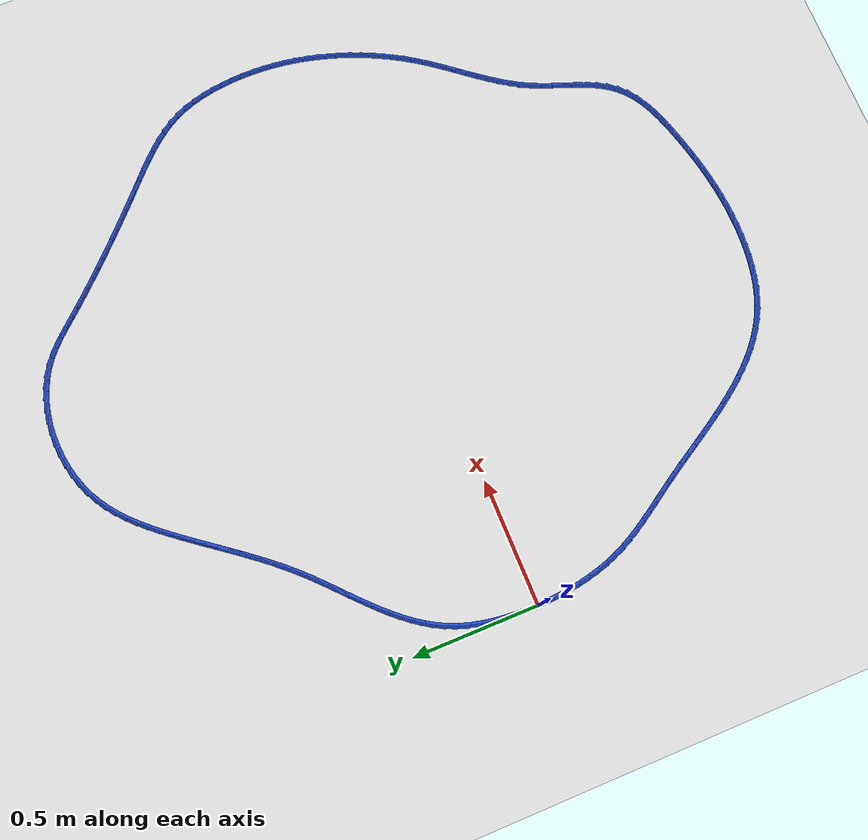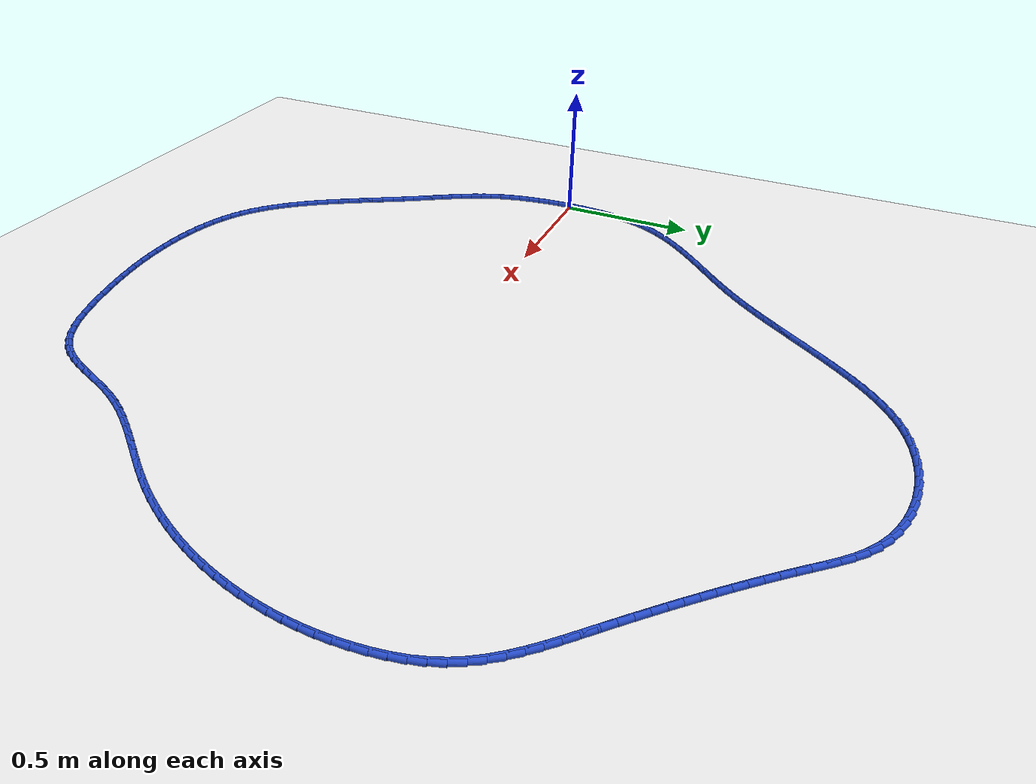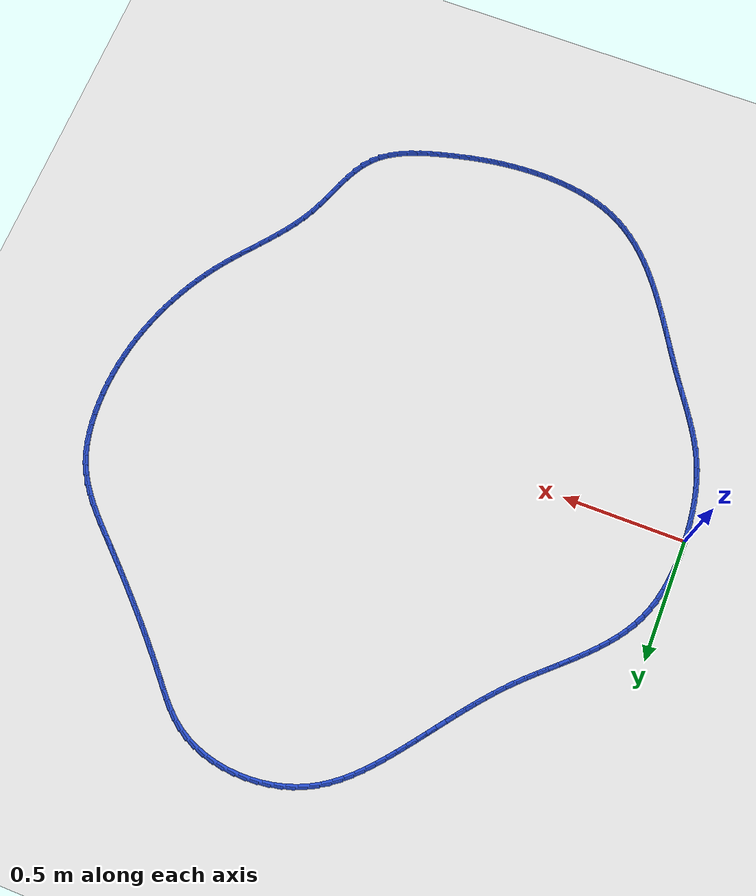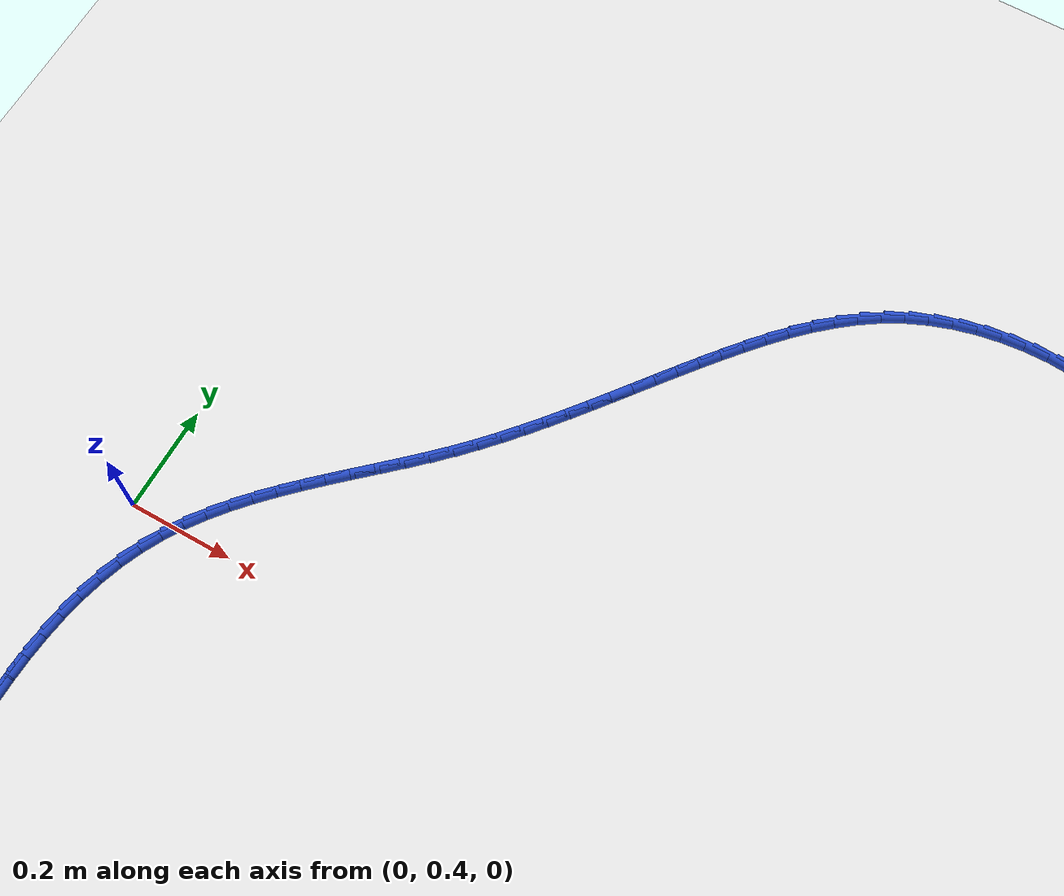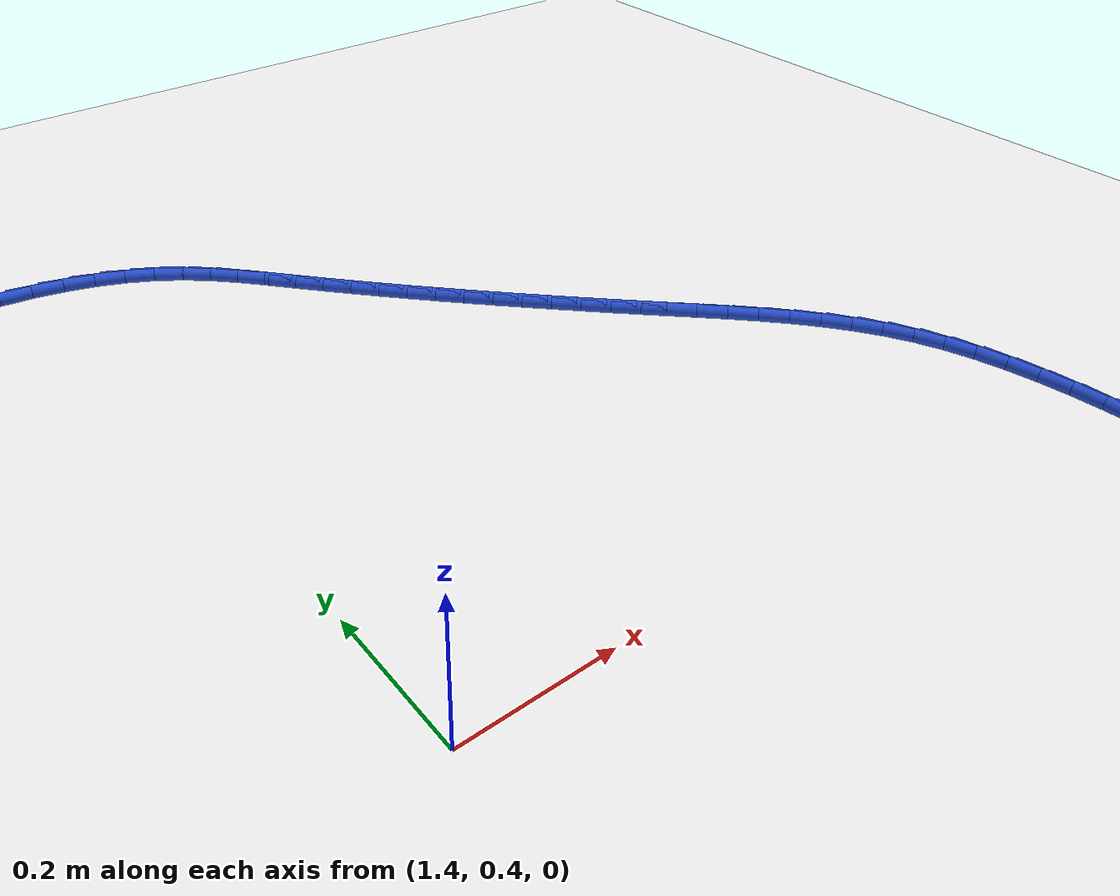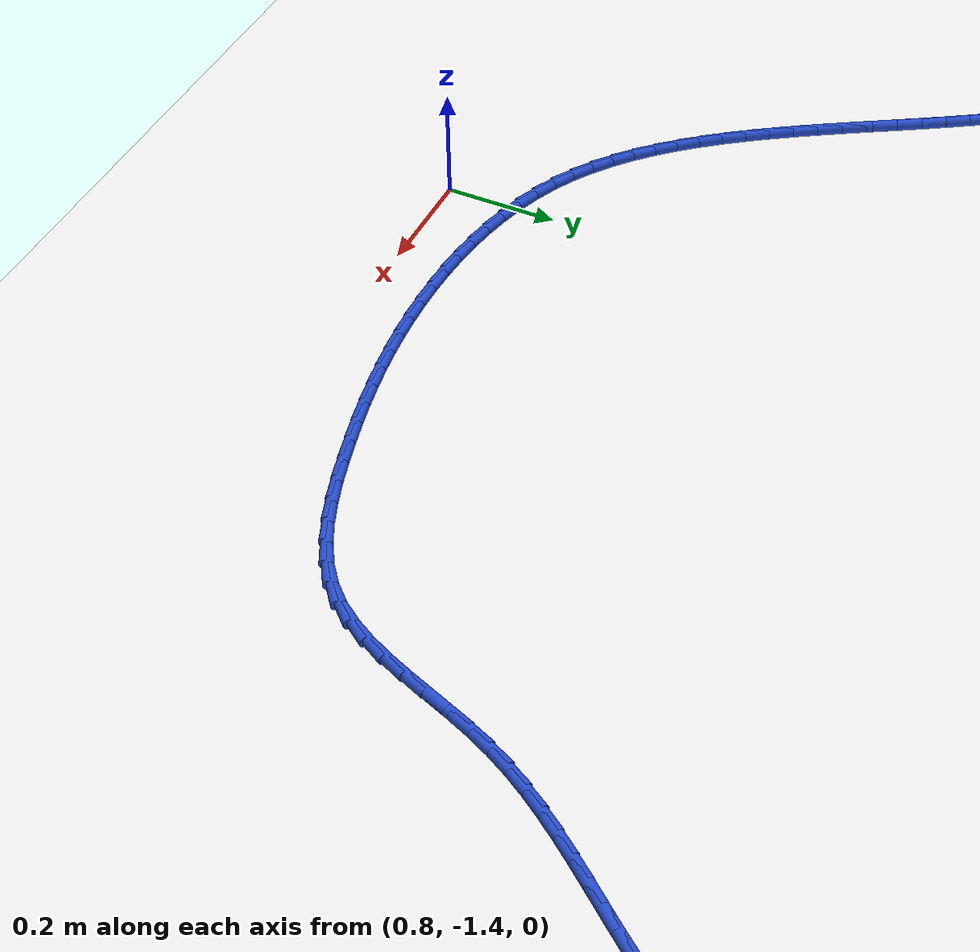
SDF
<sdf version="1.6">
 <world name="default">
  <light name="sun" type="directional">
   <pose>0 0 10 0 -0 0</pose>
   <diffuse>0.8 0.8 0.8 1</diffuse>
   <specular>0.2 0.2 0.2 1</specular>
   <attenuation>
    <range>1000</range>
    <constant>0.9</constant>
    <linear>0.01</linear>
    <quadratic>0.001</quadratic>
   </attenuation>
   <direction>-0.5 0.1 -0.9</direction>
  </light>
  <model name="ground_plane">
   <static>1</static>
   <link name="link">
    <collision name="collision">
     <geometry><plane><normal>0 0 1</normal><size>100 100</size></plane></geometry>
     <surface><friction><ode><mu>100</mu><mu2>50</mu2></ode></friction></surface>
    </collision>
    <visual name="visual">
     <cast_shadows>0</cast_shadows>
     <geometry><plane><normal>0 0 1</normal><size>100 100</size></plane></geometry>
     <material>
      <script><uri>file://media/materials/scripts/gazebo.material</uri><name>Gazebo/WhiteGlow</name></script>
     </material>
    </visual>
   </link>
  </model>
  <gravity>0 0 -9.8</gravity>
  <magnetic_field>6e-06 2.3e-05 -4.2e-05</magnetic_field>
  <atmosphere type="adiabatic"/>
  <physics name="default_physics" default="0" type="ode">
   <max_step_size>0.001</max_step_size>
   <real_time_factor>1</real_time_factor>
   <real_time_update_rate>1000</real_time_update_rate>
  </physics>
  <scene><ambient>0.4 0.4 0.4 1</ambient><background>0.7 0.7 0.7 1</background><shadows>1</shadows></scene>
  <spherical_coordinates>
   <surface_model>EARTH_WGS84</surface_model>
   <latitude_deg>0</latitude_deg>
   <longitude_deg>0</longitude_deg>
   <elevation>0</elevation>
   <heading_deg>0</heading_deg>
  </spherical_coordinates>
  <model name="line">
   <link name="link_0">
    <pose>4.0766001685454967e-17 7.632783294297951e-17 0.01 0 1.57 1.5652851152833045</pose>
    <collision name="collision">
     <geometry><cylinder><radius>0.01</radius><length>0.08</length></cylinder></geometry>
    </collision>
    <visual name="visual">
     <material>
      <script><name>Gazebo/Blue</name><uri>file://media/materials/scripts/gazebo.material</uri></script>
     </material>
     <geometry><cylinder><radius>0.01</radius><length>0.08</length></cylinder></geometry>
    </visual>
   </link>
   <link name="link_1">
    <pose>0.0002442823026844684 0.04432416156290146 0.01 0 1.57 1.5285700825561106</pose>
    <collision name="collision">
     <geometry><cylinder><radius>0.01</radius><length>0.08</length></cylinder></geometry>
    </collision>
    <visual name="visual">
     <material>
      <script><name>Gazebo/Blue</name><uri>file://media/materials/scripts/gazebo.material</uri></script>
     </material>
     <geometry><cylinder><radius>0.01</radius><length>0.08</length></cylinder></geometry>
    </visual>
   </link>
   <link name="link_2">
    <pose>0.0021137997442603595 0.0885716714209829 0.01 0 1.57 1.4867115894773664</pose>
    <collision name="collision">
     <geometry><cylinder><radius>0.01</radius><length>0.08</length></cylinder></geometry>
    </collision>
    <visual name="visual">
     <material>
      <script><name>Gazebo/Blue</name><uri>file://media/materials/scripts/gazebo.material</uri></script>
     </material>
     <geometry><cylinder><radius>0.01</radius><length>0.08</length></cylinder></geometry>
    </visual>
   </link>
   <link name="link_3">
    <pose>0.005817198089762839 0.13251146800237734 0.01 0 1.57 1.4391703211880926</pose>
    <collision name="collision">
     <geometry><cylinder><radius>0.01</radius><length>0.08</length></cylinder></geometry>
    </collision>
    <visual name="visual">
     <material>
      <script><name>Gazebo/Blue</name><uri>file://media/materials/scripts/gazebo.material</uri></script>
     </material>
     <geometry><cylinder><radius>0.01</radius><length>0.08</length></cylinder></geometry>
    </visual>
   </link>
   <link name="link_4">
    <pose>0.011563123104227031 0.17591248973521792 0.01 0 1.57 1.385363397241208</pose>
    <collision name="collision">
     <geometry><cylinder><radius>0.01</radius><length>0.08</length></cylinder></geometry>
    </collision>
    <visual name="visual">
     <material>
      <script><name>Gazebo/Blue</name><uri>file://media/materials/scripts/gazebo.material</uri></script>
     </material>
     <geometry><cylinder><radius>0.01</radius><length>0.08</length></cylinder></geometry>
    </visual>
   </link>
   <link name="link_5">
    <pose>0.01956022055268805 0.21854367504763758 0.01 0 1.57 1.324702411401661</pose>
    <collision name="collision">
     <geometry><cylinder><radius>0.01</radius><length>0.08</length></cylinder></geometry>
    </collision>
    <visual name="visual">
     <material>
      <script><name>Gazebo/Blue</name><uri>file://media/materials/scripts/gazebo.material</uri></script>
     </material>
     <geometry><cylinder><radius>0.01</radius><length>0.08</length></cylinder></geometry>
    </visual>
   </link>
   <link name="link_6">
    <pose>0.030017136200181007 0.2601739623677694 0.01 0 1.57 1.2566557070892985</pose>
    <collision name="collision">
     <geometry><cylinder><radius>0.01</radius><length>0.08</length></cylinder></geometry>
    </collision>
    <visual name="visual">
     <material>
      <script><name>Gazebo/Blue</name><uri>file://media/materials/scripts/gazebo.material</uri></script>
     </material>
     <geometry><cylinder><radius>0.01</radius><length>0.08</length></cylinder></geometry>
    </visual>
   </link>
   <link name="link_7">
    <pose>0.043142515811741056 0.3005722901237463 0.01 0 1.57 1.1808415843914173</pose>
    <collision name="collision">
     <geometry><cylinder><radius>0.01</radius><length>0.08</length></cylinder></geometry>
    </collision>
    <visual name="visual">
     <material>
      <script><name>Gazebo/Blue</name><uri>file://media/materials/scripts/gazebo.material</uri></script>
     </material>
     <geometry><cylinder><radius>0.01</radius><length>0.08</length></cylinder></geometry>
    </visual>
   </link>
   <link name="link_8">
    <pose>0.059145005152403285 0.3395075967437015 0.01 0 1.57 1.099297835576982</pose>
    <collision name="collision">
     <geometry><cylinder><radius>0.01</radius><length>0.08</length></cylinder></geometry>
    </collision>
    <visual name="visual">
     <material>
      <script><name>Gazebo/Blue</name><uri>file://media/materials/scripts/gazebo.material</uri></script>
     </material>
     <geometry><cylinder><radius>0.01</radius><length>0.08</length></cylinder></geometry>
    </visual>
   </link>
   <link name="link_9">
    <pose>0.07816109508705557 0.37680483596662545 0.01 0 1.57 1.0230116683269173</pose>
    <collision name="collision">
     <geometry><cylinder><radius>0.01</radius><length>0.08</length></cylinder></geometry>
    </collision>
    <visual name="visual">
     <material>
      <script><name>Gazebo/Blue</name><uri>file://media/materials/scripts/gazebo.material</uri></script>
     </material>
     <geometry><cylinder><radius>0.01</radius><length>0.08</length></cylinder></geometry>
    </visual>
   </link>
   <link name="link_10">
    <pose>0.09997528811176017 0.4125622172335854 0.01 0 1.57 0.9559776037493904</pose>
    <collision name="collision">
     <geometry><cylinder><radius>0.01</radius><length>0.08</length></cylinder></geometry>
    </collision>
    <visual name="visual">
     <material>
      <script><name>Gazebo/Blue</name><uri>file://media/materials/scripts/gazebo.material</uri></script>
     </material>
     <geometry><cylinder><radius>0.01</radius><length>0.08</length></cylinder></geometry>
    </visual>
   </link>
   <link name="link_11">
    <pose>0.12426491600606802 0.446961148784177 0.01 0 1.57 0.8985410213835947</pose>
    <collision name="collision">
     <geometry><cylinder><radius>0.01</radius><length>0.08</length></cylinder></geometry>
    </collision>
    <visual name="visual">
     <material>
      <script><name>Gazebo/Blue</name><uri>file://media/materials/scripts/gazebo.material</uri></script>
     </material>
     <geometry><cylinder><radius>0.01</radius><length>0.08</length></cylinder></geometry>
    </visual>
   </link>
   <link name="link_12">
    <pose>0.1507072850935169 0.48018305862001487 0.01 0 1.57 0.8506604310701336</pose>
    <collision name="collision">
     <geometry><cylinder><radius>0.01</radius><length>0.08</length></cylinder></geometry>
    </collision>
    <visual name="visual">
     <material>
      <script><name>Gazebo/Blue</name><uri>file://media/materials/scripts/gazebo.material</uri></script>
     </material>
     <geometry><cylinder><radius>0.01</radius><length>0.08</length></cylinder></geometry>
    </visual>
   </link>
   <link name="link_13">
    <pose>0.17897970169764468 0.5124093747427135 0.01 0 1.57 0.81206823507241</pose>
    <collision name="collision">
     <geometry><cylinder><radius>0.01</radius><length>0.08</length></cylinder></geometry>
    </collision>
    <visual name="visual">
     <material>
      <script><name>Gazebo/Blue</name><uri>file://media/materials/scripts/gazebo.material</uri></script>
     </material>
     <geometry><cylinder><radius>0.01</radius><length>0.08</length></cylinder></geometry>
    </visual>
   </link>
   <link name="link_14">
    <pose>0.20875947214198903 0.5438215251538879 0.01 0 1.57 0.7824016321945504</pose>
    <collision name="collision">
     <geometry><cylinder><radius>0.01</radius><length>0.08</length></cylinder></geometry>
    </collision>
    <visual name="visual">
     <material>
      <script><name>Gazebo/Blue</name><uri>file://media/materials/scripts/gazebo.material</uri></script>
     </material>
     <geometry><cylinder><radius>0.01</radius><length>0.08</length></cylinder></geometry>
    </visual>
   </link>
   <link name="link_15">
    <pose>0.23972390275008787 0.5746009378551522 0.01 0 1.57 0.7612968677047302</pose>
    <collision name="collision">
     <geometry><cylinder><radius>0.01</radius><length>0.08</length></cylinder></geometry>
    </collision>
    <visual name="visual">
     <material>
      <script><name>Gazebo/Blue</name><uri>file://media/materials/scripts/gazebo.material</uri></script>
     </material>
     <geometry><cylinder><radius>0.01</radius><length>0.08</length></cylinder></geometry>
    </visual>
   </link>
   <link name="link_16">
    <pose>0.2715502998454788 0.6049290408481215 0.01 0 1.57 0.7484507942404208</pose>
    <collision name="collision">
     <geometry><cylinder><radius>0.01</radius><length>0.08</length></cylinder></geometry>
    </collision>
    <visual name="visual">
     <material>
      <script><name>Gazebo/Blue</name><uri>file://media/materials/scripts/gazebo.material</uri></script>
     </material>
     <geometry><cylinder><radius>0.01</radius><length>0.08</length></cylinder></geometry>
    </visual>
   </link>
   <link name="link_17">
    <pose>0.3039159697516995 0.6349872621344094 0.01 0 1.57 0.7436574778819449</pose>
    <collision name="collision">
     <geometry><cylinder><radius>0.01</radius><length>0.08</length></cylinder></geometry>
    </collision>
    <visual name="visual">
     <material>
      <script><name>Gazebo/Blue</name><uri>file://media/materials/scripts/gazebo.material</uri></script>
     </material>
     <geometry><cylinder><radius>0.01</radius><length>0.08</length></cylinder></geometry>
    </visual>
   </link>
   <link name="link_18">
    <pose>0.3364982187922882 0.6649570297156315 0.01 0 1.57 0.7468270247068363</pose>
    <collision name="collision">
     <geometry><cylinder><radius>0.01</radius><length>0.08</length></cylinder></geometry>
    </collision>
    <visual name="visual">
     <material>
      <script><name>Gazebo/Blue</name><uri>file://media/materials/scripts/gazebo.material</uri></script>
     </material>
     <geometry><cylinder><radius>0.01</radius><length>0.08</length></cylinder></geometry>
    </visual>
   </link>
   <link name="link_19">
    <pose>0.3689743532907821 0.695019771593402 0.01 0 1.57 0.7579914405183313</pose>
    <collision name="collision">
     <geometry><cylinder><radius>0.01</radius><length>0.08</length></cylinder></geometry>
    </collision>
    <visual name="visual">
     <material>
      <script><name>Gazebo/Blue</name><uri>file://media/materials/scripts/gazebo.material</uri></script>
     </material>
     <geometry><cylinder><radius>0.01</radius><length>0.08</length></cylinder></geometry>
    </visual>
   </link>
   <link name="link_20">
    <pose>0.4010216795707194 0.7253569157693355 0.01 0 1.57 0.7772994575990935</pose>
    <collision name="collision">
     <geometry><cylinder><radius>0.01</radius><length>0.08</length></cylinder></geometry>
    </collision>
    <visual name="visual">
     <material>
      <script><name>Gazebo/Blue</name><uri>file://media/materials/scripts/gazebo.material</uri></script>
     </material>
     <geometry><cylinder><radius>0.01</radius><length>0.08</length></cylinder></geometry>
    </visual>
   </link>
   <link name="link_21">
    <pose>0.4323175039556376 0.7561498902450466 0.01 0 1.57 0.8044462042061874</pose>
    <collision name="collision">
     <geometry><cylinder><radius>0.01</radius><length>0.08</length></cylinder></geometry>
    </collision>
    <visual name="visual">
     <material>
      <script><name>Gazebo/Blue</name><uri>file://media/materials/scripts/gazebo.material</uri></script>
     </material>
     <geometry><cylinder><radius>0.01</radius><length>0.08</length></cylinder></geometry>
    </visual>
   </link>
   <link name="link_22">
    <pose>0.46256096367066835 0.787568024591761 0.01 0 1.57 0.8327519605443752</pose>
    <collision name="collision">
     <geometry><cylinder><radius>0.01</radius><length>0.08</length></cylinder></geometry>
    </collision>
    <visual name="visual">
     <material>
      <script><name>Gazebo/Blue</name><uri>file://media/materials/scripts/gazebo.material</uri></script>
     </material>
     <geometry><cylinder><radius>0.01</radius><length>0.08</length></cylinder></geometry>
    </visual>
   </link>
   <link name="link_23">
    <pose>0.4917221097521488 0.8196305111143997 0.01 0 1.57 0.8574478159559658</pose>
    <collision name="collision">
     <geometry><cylinder><radius>0.01</radius><length>0.08</length></cylinder></geometry>
    </collision>
    <visual name="visual">
     <material>
      <script><name>Gazebo/Blue</name><uri>file://media/materials/scripts/gazebo.material</uri></script>
     </material>
     <geometry><cylinder><radius>0.01</radius><length>0.08</length></cylinder></geometry>
    </visual>
   </link>
   <link name="link_24">
    <pose>0.5199542696768519 0.8522549724576928 0.01 0 1.57 0.8782935683910906</pose>
    <collision name="collision">
     <geometry><cylinder><radius>0.01</radius><length>0.08</length></cylinder></geometry>
    </collision>
    <visual name="visual">
     <material>
      <script><name>Gazebo/Blue</name><uri>file://media/materials/scripts/gazebo.material</uri></script>
     </material>
     <geometry><cylinder><radius>0.01</radius><length>0.08</length></cylinder></geometry>
    </visual>
   </link>
   <link name="link_25">
    <pose>0.5474142308248384 0.8853571138284262 0.01 0 1.57 0.8951798627621346</pose>
    <collision name="collision">
     <geometry><cylinder><radius>0.01</radius><length>0.08</length></cylinder></geometry>
    </collision>
    <visual name="visual">
     <material>
      <script><name>Gazebo/Blue</name><uri>file://media/materials/scripts/gazebo.material</uri></script>
     </material>
     <geometry><cylinder><radius>0.01</radius><length>0.08</length></cylinder></geometry>
    </visual>
   </link>
   <link name="link_26">
    <pose>0.5742587805761694 0.9188526404333854 0.01 0 1.57 0.9080330977251189</pose>
    <collision name="collision">
     <geometry><cylinder><radius>0.01</radius><length>0.08</length></cylinder></geometry>
    </collision>
    <visual name="visual">
     <material>
      <script><name>Gazebo/Blue</name><uri>file://media/materials/scripts/gazebo.material</uri></script>
     </material>
     <geometry><cylinder><radius>0.01</radius><length>0.08</length></cylinder></geometry>
    </visual>
   </link>
   <link name="link_27">
    <pose>0.6006447063109055 0.9526572574793559 0.01 0 1.57 0.9168085045590214</pose>
    <collision name="collision">
     <geometry><cylinder><radius>0.01</radius><length>0.08</length></cylinder></geometry>
    </collision>
    <visual name="visual">
     <material>
      <script><name>Gazebo/Blue</name><uri>file://media/materials/scripts/gazebo.material</uri></script>
     </material>
     <geometry><cylinder><radius>0.01</radius><length>0.08</length></cylinder></geometry>
    </visual>
   </link>
   <link name="link_28">
    <pose>0.6267287954091073 0.9866866701731235 0.01 0 1.57 0.9214843861114103</pose>
    <collision name="collision">
     <geometry><cylinder><radius>0.01</radius><length>0.08</length></cylinder></geometry>
    </collision>
    <visual name="visual">
     <material>
      <script><name>Gazebo/Blue</name><uri>file://media/materials/scripts/gazebo.material</uri></script>
     </material>
     <geometry><cylinder><radius>0.01</radius><length>0.08</length></cylinder></geometry>
    </visual>
   </link>
   <link name="link_29">
    <pose>0.6526678352508362 1.0208565837214745 0.01 0 1.57 0.9220579324590353</pose>
    <collision name="collision">
     <geometry><cylinder><radius>0.01</radius><length>0.08</length></cylinder></geometry>
    </collision>
    <visual name="visual">
     <material>
      <script><name>Gazebo/Blue</name><uri>file://media/materials/scripts/gazebo.material</uri></script>
     </material>
     <geometry><cylinder><radius>0.01</radius><length>0.08</length></cylinder></geometry>
    </visual>
   </link>
   <link name="link_30">
    <pose>0.6786186132161524 1.0550827033311938 0.01 0 1.57 0.9185428458880102</pose>
    <collision name="collision">
     <geometry><cylinder><radius>0.01</radius><length>0.08</length></cylinder></geometry>
    </collision>
    <visual name="visual">
     <material>
      <script><name>Gazebo/Blue</name><uri>file://media/materials/scripts/gazebo.material</uri></script>
     </material>
     <geometry><cylinder><radius>0.01</radius><length>0.08</length></cylinder></geometry>
    </visual>
   </link>
   <link name="link_31">
    <pose>0.7047379166851168 1.0892807342090671 0.01 0 1.57 0.9109688613331384</pose>
    <collision name="collision">
     <geometry><cylinder><radius>0.01</radius><length>0.08</length></cylinder></geometry>
    </collision>
    <visual name="visual">
     <material>
      <script><name>Gazebo/Blue</name><uri>file://media/materials/scripts/gazebo.material</uri></script>
     </material>
     <geometry><cylinder><radius>0.01</radius><length>0.08</length></cylinder></geometry>
    </visual>
   </link>
   <link name="link_32">
    <pose>0.7311825330377906 1.1233663815618808 0.01 0 1.57 0.8993831275105147</pose>
    <collision name="collision">
     <geometry><cylinder><radius>0.01</radius><length>0.08</length></cylinder></geometry>
    </collision>
    <visual name="visual">
     <material>
      <script><name>Gazebo/Blue</name><uri>file://media/materials/scripts/gazebo.material</uri></script>
     </material>
     <geometry><cylinder><radius>0.01</radius><length>0.08</length></cylinder></geometry>
    </visual>
   </link>
   <link name="link_33">
    <pose>0.7581092496542342 1.15725535059642 0.01 0 1.57 0.8835134176179522</pose>
    <collision name="collision">
     <geometry><cylinder><radius>0.01</radius><length>0.08</length></cylinder></geometry>
    </collision>
    <visual name="visual">
     <material>
      <script><name>Gazebo/Blue</name><uri>file://media/materials/scripts/gazebo.material</uri></script>
     </material>
     <geometry><cylinder><radius>0.01</radius><length>0.08</length></cylinder></geometry>
    </visual>
   </link>
   <link name="link_34">
    <pose>0.7856785567800937 1.190844571792792 0.01 0 1.57 0.8600492522311644</pose>
    <collision name="collision">
     <geometry><cylinder><radius>0.01</radius><length>0.08</length></cylinder></geometry>
    </collision>
    <visual name="visual">
     <material>
      <script><name>Gazebo/Blue</name><uri>file://media/materials/scripts/gazebo.material</uri></script>
     </material>
     <geometry><cylinder><radius>0.01</radius><length>0.08</length></cylinder></geometry>
    </visual>
   </link>
   <link name="link_35">
    <pose>0.8140873707989972 1.223846283324869 0.01 0 1.57 0.826936648480917</pose>
    <collision name="collision">
     <geometry><cylinder><radius>0.01</radius><length>0.08</length></cylinder></geometry>
    </collision>
    <visual name="visual">
     <material>
      <script><name>Gazebo/Blue</name><uri>file://media/materials/scripts/gazebo.material</uri></script>
     </material>
     <geometry><cylinder><radius>0.01</radius><length>0.08</length></cylinder></geometry>
    </visual>
   </link>
   <link name="link_36">
    <pose>0.8435533051634754 1.255867782530097 0.01 0 1.57 0.7838745705546857</pose>
    <collision name="collision">
     <geometry><cylinder><radius>0.01</radius><length>0.08</length></cylinder></geometry>
    </collision>
    <visual name="visual">
     <material>
      <script><name>Gazebo/Blue</name><uri>file://media/materials/scripts/gazebo.material</uri></script>
     </material>
     <geometry><cylinder><radius>0.01</radius><length>0.08</length></cylinder></geometry>
    </visual>
   </link>
   <link name="link_37">
    <pose>0.8742942116779341 1.2865151582247802 0.01 0 1.57 0.7305649361996965</pose>
    <collision name="collision">
     <geometry><cylinder><radius>0.01</radius><length>0.08</length></cylinder></geometry>
    </collision>
    <visual name="visual">
     <material>
      <script><name>Gazebo/Blue</name><uri>file://media/materials/scripts/gazebo.material</uri></script>
     </material>
     <geometry><cylinder><radius>0.01</radius><length>0.08</length></cylinder></geometry>
    </visual>
   </link>
   <link name="link_38">
    <pose>0.9065279421467807 1.3153944992252238 0.01 0 1.57 0.6668209497076089</pose>
    <collision name="collision">
     <geometry><cylinder><radius>0.01</radius><length>0.08</length></cylinder></geometry>
    </collision>
    <visual name="visual">
     <material>
      <script><name>Gazebo/Blue</name><uri>file://media/materials/scripts/gazebo.material</uri></script>
     </material>
     <geometry><cylinder><radius>0.01</radius><length>0.08</length></cylinder></geometry>
    </visual>
   </link>
   <link name="link_39">
    <pose>0.9404723483744215 1.3421118943477321 0.01 0 1.57 0.5927398882752486</pose>
    <collision name="collision">
     <geometry><cylinder><radius>0.01</radius><length>0.08</length></cylinder></geometry>
    </collision>
    <visual name="visual">
     <material>
      <script><name>Gazebo/Blue</name><uri>file://media/materials/scripts/gazebo.material</uri></script>
     </material>
     <geometry><cylinder><radius>0.01</radius><length>0.08</length></cylinder></geometry>
    </visual>
   </link>
   <link name="link_40">
    <pose>0.9763452821652637 1.366273432408611 0.01 0 1.57 0.5089041774875436</pose>
    <collision name="collision">
     <geometry><cylinder><radius>0.01</radius><length>0.08</length></cylinder></geometry>
    </collision>
    <visual name="visual">
     <material>
      <script><name>Gazebo/Blue</name><uri>file://media/materials/scripts/gazebo.material</uri></script>
     </material>
     <geometry><cylinder><radius>0.01</radius><length>0.08</length></cylinder></geometry>
    </visual>
   </link>
   <link name="link_41">
    <pose>1.0143645953237137 1.3874852022241648 0.01 0 1.57 0.41806926688751783</pose>
    <collision name="collision">
     <geometry><cylinder><radius>0.01</radius><length>0.08</length></cylinder></geometry>
    </collision>
    <visual name="visual">
     <material>
      <script><name>Gazebo/Blue</name><uri>file://media/materials/scripts/gazebo.material</uri></script>
     </material>
     <geometry><cylinder><radius>0.01</radius><length>0.08</length></cylinder></geometry>
    </visual>
   </link>
   <link name="link_42">
    <pose>1.0546754392531716 1.4053936479595435 0.01 0 1.57 0.3299075125731556</pose>
    <collision name="collision">
     <geometry><cylinder><radius>0.01</radius><length>0.08</length></cylinder></geometry>
    </collision>
    <visual name="visual">
     <material>
      <script><name>Gazebo/Blue</name><uri>file://media/materials/scripts/gazebo.material</uri></script>
     </material>
     <geometry><cylinder><radius>0.01</radius><length>0.08</length></cylinder></geometry>
    </visual>
   </link>
   <link name="link_43">
    <pose>1.0969927680059188 1.4198840125201544 0.01 0 1.57 0.24658156210344415</pose>
    <collision name="collision">
     <geometry><cylinder><radius>0.01</radius><length>0.08</length></cylinder></geometry>
    </collision>
    <visual name="visual">
     <material>
      <script><name>Gazebo/Blue</name><uri>file://media/materials/scripts/gazebo.material</uri></script>
     </material>
     <geometry><cylinder><radius>0.01</radius><length>0.08</length></cylinder></geometry>
    </visual>
   </link>
   <link name="link_44">
    <pose>1.1408738780967633 1.4309290531144168 0.01 0 1.57 0.16671103317510894</pose>
    <collision name="collision">
     <geometry><cylinder><radius>0.01</radius><length>0.08</length></cylinder></geometry>
    </collision>
    <visual name="visual">
     <material>
      <script><name>Gazebo/Blue</name><uri>file://media/materials/scripts/gazebo.material</uri></script>
     </material>
     <geometry><cylinder><radius>0.01</radius><length>0.08</length></cylinder></geometry>
    </visual>
   </link>
   <link name="link_45">
    <pose>1.1858758280295978 1.4385016590685002 0.01 0 1.57 0.08893019031619626</pose>
    <collision name="collision">
     <geometry><cylinder><radius>0.01</radius><length>0.08</length></cylinder></geometry>
    </collision>
    <visual name="visual">
     <material>
      <script><name>Gazebo/Blue</name><uri>file://media/materials/scripts/gazebo.material</uri></script>
     </material>
     <geometry><cylinder><radius>0.01</radius><length>0.08</length></cylinder></geometry>
    </visual>
   </link>
   <link name="link_46">
    <pose>1.2315556763083166 1.4425747197085748 0.01 0 1.57 0.011899840564138219</pose>
    <collision name="collision">
     <geometry><cylinder><radius>0.01</radius><length>0.08</length></cylinder></geometry>
    </collision>
    <visual name="visual">
     <material>
      <script><name>Gazebo/Blue</name><uri>file://media/materials/scripts/gazebo.material</uri></script>
     </material>
     <geometry><cylinder><radius>0.01</radius><length>0.08</length></cylinder></geometry>
    </visual>
   </link>
   <link name="link_47">
    <pose>1.2774704814368125 1.4431211243608106 0.01 0 1.57 -0.06570208504036454</pose>
    <collision name="collision">
     <geometry><cylinder><radius>0.01</radius><length>0.08</length></cylinder></geometry>
    </collision>
    <visual name="visual">
     <material>
      <script><name>Gazebo/Blue</name><uri>file://media/materials/scripts/gazebo.material</uri></script>
     </material>
     <geometry><cylinder><radius>0.01</radius><length>0.08</length></cylinder></geometry>
    </visual>
   </link>
   <link name="link_48">
    <pose>1.32317730191898 1.440113762351378 0.01 0 1.57 -0.14519470935208256</pose>
    <collision name="collision">
     <geometry><cylinder><radius>0.01</radius><length>0.08</length></cylinder></geometry>
    </collision>
    <visual name="visual">
     <material>
      <script><name>Gazebo/Blue</name><uri>file://media/materials/scripts/gazebo.material</uri></script>
     </material>
     <geometry><cylinder><radius>0.01</radius><length>0.08</length></cylinder></geometry>
    </visual>
   </link>
   <link name="link_49">
    <pose>1.3682331962587129 1.4335255230064468 0.01 0 1.57 -0.22790311764480517</pose>
    <collision name="collision">
     <geometry><cylinder><radius>0.01</radius><length>0.08</length></cylinder></geometry>
    </collision>
    <visual name="visual">
     <material>
      <script><name>Gazebo/Blue</name><uri>file://media/materials/scripts/gazebo.material</uri></script>
     </material>
     <geometry><cylinder><radius>0.01</radius><length>0.08</length></cylinder></geometry>
    </visual>
   </link>
   <link name="link_50">
    <pose>1.412195222959903 1.4233292956521861 0.01 0 1.57 -0.3151511222260228</pose>
    <collision name="collision">
     <geometry><cylinder><radius>0.01</radius><length>0.08</length></cylinder></geometry>
    </collision>
    <visual name="visual">
     <material>
      <script><name>Gazebo/Blue</name><uri>file://media/materials/scripts/gazebo.material</uri></script>
     </material>
     <geometry><cylinder><radius>0.01</radius><length>0.08</length></cylinder></geometry>
    </visual>
   </link>
   <link name="link_51">
    <pose>1.4546204405264458 1.4094979696147671 0.01 0 1.57 -0.4082241657953518</pose>
    <collision name="collision">
     <geometry><cylinder><radius>0.01</radius><length>0.08</length></cylinder></geometry>
    </collision>
    <visual name="visual">
     <material>
      <script><name>Gazebo/Blue</name><uri>file://media/materials/scripts/gazebo.material</uri></script>
     </material>
     <geometry><cylinder><radius>0.01</radius><length>0.08</length></cylinder></geometry>
    </visual>
   </link>
   <link name="link_52">
    <pose>1.4950659074622346 1.392004434220359 0.01 0 1.57 -0.50828529681921</pose>
    <collision name="collision">
     <geometry><cylinder><radius>0.01</radius><length>0.08</length></cylinder></geometry>
    </collision>
    <visual name="visual">
     <material>
      <script><name>Gazebo/Blue</name><uri>file://media/materials/scripts/gazebo.material</uri></script>
     </material>
     <geometry><cylinder><radius>0.01</radius><length>0.08</length></cylinder></geometry>
    </visual>
   </link>
   <link name="link_53">
    <pose>1.5330886822711618 1.3708215787951321 0.01 0 1.57 -0.6154524122041676</pose>
    <collision name="collision">
     <geometry><cylinder><radius>0.01</radius><length>0.08</length></cylinder></geometry>
    </collision>
    <visual name="visual">
     <material>
      <script><name>Gazebo/Blue</name><uri>file://media/materials/scripts/gazebo.material</uri></script>
     </material>
     <geometry><cylinder><radius>0.01</radius><length>0.08</length></cylinder></geometry>
    </visual>
   </link>
   <link name="link_54">
    <pose>1.568272867532319 1.3459440433845258 0.01 0 1.57 -0.7133078720711875</pose>
    <collision name="collision">
     <geometry><cylinder><radius>0.01</radius><length>0.08</length></cylinder></geometry>
    </collision>
    <visual name="visual">
     <material>
      <script><name>Gazebo/Blue</name><uri>file://media/materials/scripts/gazebo.material</uri></script>
     </material>
     <geometry><cylinder><radius>0.01</radius><length>0.08</length></cylinder></geometry>
    </visual>
   </link>
   <link name="link_55">
    <pose>1.6007709232331055 1.3178235804455725 0.01 0 1.57 -0.7849528757141836</pose>
    <collision name="collision">
     <geometry><cylinder><radius>0.01</radius><length>0.08</length></cylinder></geometry>
    </collision>
    <visual name="visual">
     <material>
      <script><name>Gazebo/Blue</name><uri>file://media/materials/scripts/gazebo.material</uri></script>
     </material>
     <geometry><cylinder><radius>0.01</radius><length>0.08</length></cylinder></geometry>
    </visual>
   </link>
   <link name="link_56">
    <pose>1.6312753652719412 1.2873462928216546 0.01 0 1.57 -0.8296186448521206</pose>
    <collision name="collision">
     <geometry><cylinder><radius>0.01</radius><length>0.08</length></cylinder></geometry>
    </collision>
    <visual name="visual">
     <material>
      <script><name>Gazebo/Blue</name><uri>file://media/materials/scripts/gazebo.material</uri></script>
     </material>
     <geometry><cylinder><radius>0.01</radius><length>0.08</length></cylinder></geometry>
    </visual>
   </link>
   <link name="link_57">
    <pose>1.6605000886932886 1.255415477946849 0.01 0 1.57 -0.8478316088885182</pose>
    <collision name="collision">
     <geometry><cylinder><radius>0.01</radius><length>0.08</length></cylinder></geometry>
    </collision>
    <visual name="visual">
     <material>
      <script><name>Gazebo/Blue</name><uri>file://media/materials/scripts/gazebo.material</uri></script>
     </material>
     <geometry><cylinder><radius>0.01</radius><length>0.08</length></cylinder></geometry>
    </visual>
   </link>
   <link name="link_58">
    <pose>1.6891589885416112 1.2229344332552343 0.01 0 1.57 -0.8435478911876069</pose>
    <collision name="collision">
     <geometry><cylinder><radius>0.01</radius><length>0.08</length></cylinder></geometry>
    </collision>
    <visual name="visual">
     <material>
      <script><name>Gazebo/Blue</name><uri>file://media/materials/scripts/gazebo.material</uri></script>
     </material>
     <geometry><cylinder><radius>0.01</radius><length>0.08</length></cylinder></geometry>
    </visual>
   </link>
   <link name="link_59">
    <pose>1.7178680344702557 1.1906761525251786 0.01 0 1.57 -0.8343294019616448</pose>
    <collision name="collision">
     <geometry><cylinder><radius>0.01</radius><length>0.08</length></cylinder></geometry>
    </collision>
    <visual name="visual">
     <material>
      <script><name>Gazebo/Blue</name><uri>file://media/materials/scripts/gazebo.material</uri></script>
     </material>
     <geometry><cylinder><radius>0.01</radius><length>0.08</length></cylinder></geometry>
    </visual>
   </link>
   <link name="link_60">
    <pose>1.7467756614256493 1.1587915081343765 0.01 0 1.57 -0.8254408898371693</pose>
    <collision name="collision">
     <geometry><cylinder><radius>0.01</radius><length>0.08</length></cylinder></geometry>
    </collision>
    <visual name="visual">
     <material>
      <script><name>Gazebo/Blue</name><uri>file://media/materials/scripts/gazebo.material</uri></script>
     </material>
     <geometry><cylinder><radius>0.01</radius><length>0.08</length></cylinder></geometry>
    </visual>
   </link>
   <link name="link_61">
    <pose>1.775890929621333 1.1272459145624045 0.01 0 1.57 -0.8169069097646682</pose>
    <collision name="collision">
     <geometry><cylinder><radius>0.01</radius><length>0.08</length></cylinder></geometry>
    </collision>
    <visual name="visual">
     <material>
      <script><name>Gazebo/Blue</name><uri>file://media/materials/scripts/gazebo.material</uri></script>
     </material>
     <geometry><cylinder><radius>0.01</radius><length>0.08</length></cylinder></geometry>
    </visual>
   </link>
   <link name="link_62">
    <pose>1.8052228752988861 1.096004754390736 0.01 0 1.57 -0.8087494122857563</pose>
    <collision name="collision">
     <geometry><cylinder><radius>0.01</radius><length>0.08</length></cylinder></geometry>
    </collision>
    <visual name="visual">
     <material>
      <script><name>Gazebo/Blue</name><uri>file://media/materials/scripts/gazebo.material</uri></script>
     </material>
     <geometry><cylinder><radius>0.01</radius><length>0.08</length></cylinder></geometry>
    </visual>
   </link>
   <link name="link_63">
    <pose>1.834780534699888 1.065033410200845 0.01 0 1.57 -0.8009884876425595</pose>
    <collision name="collision">
     <geometry><cylinder><radius>0.01</radius><length>0.08</length></cylinder></geometry>
    </collision>
    <visual name="visual">
     <material>
      <script><name>Gazebo/Blue</name><uri>file://media/materials/scripts/gazebo.material</uri></script>
     </material>
     <geometry><cylinder><radius>0.01</radius><length>0.08</length></cylinder></geometry>
    </visual>
   </link>
   <link name="link_64">
    <pose>1.8645729440659167 1.0342972645742048 0.01 0 1.57 -0.793642229537139</pose>
    <collision name="collision">
     <geometry><cylinder><radius>0.01</radius><length>0.08</length></cylinder></geometry>
    </collision>
    <visual name="visual">
     <material>
      <script><name>Gazebo/Blue</name><uri>file://media/materials/scripts/gazebo.material</uri></script>
     </material>
     <geometry><cylinder><radius>0.01</radius><length>0.08</length></cylinder></geometry>
    </visual>
   </link>
   <link name="link_65">
    <pose>1.894609139638553 1.0037617000922896 0.01 0 1.57 -0.7867266256854948</pose>
    <collision name="collision">
     <geometry><cylinder><radius>0.01</radius><length>0.08</length></cylinder></geometry>
    </collision>
    <visual name="visual">
     <material>
      <script><name>Gazebo/Blue</name><uri>file://media/materials/scripts/gazebo.material</uri></script>
     </material>
     <geometry><cylinder><radius>0.01</radius><length>0.08</length></cylinder></geometry>
    </visual>
   </link>
   <link name="link_66">
    <pose>1.9248981576593756 0.9733920993365729 0.01 0 1.57 -0.7802554758712065</pose>
    <collision name="collision">
     <geometry><cylinder><radius>0.01</radius><length>0.08</length></cylinder></geometry>
    </collision>
    <visual name="visual">
     <material>
      <script><name>Gazebo/Blue</name><uri>file://media/materials/scripts/gazebo.material</uri></script>
     </material>
     <geometry><cylinder><radius>0.01</radius><length>0.08</length></cylinder></geometry>
    </visual>
   </link>
   <link name="link_67">
    <pose>1.9554490343699633 0.9431538448885287 0.01 0 1.57 -0.7742403375500369</pose>
    <collision name="collision">
     <geometry><cylinder><radius>0.01</radius><length>0.08</length></cylinder></geometry>
    </collision>
    <visual name="visual">
     <material>
      <script><name>Gazebo/Blue</name><uri>file://media/materials/scripts/gazebo.material</uri></script>
     </material>
     <geometry><cylinder><radius>0.01</radius><length>0.08</length></cylinder></geometry>
    </visual>
   </link>
   <link name="link_68">
    <pose>1.986270806011896 0.9130123193296309 0.01 0 1.57 -0.7686904984523881</pose>
    <collision name="collision">
     <geometry><cylinder><radius>0.01</radius><length>0.08</length></cylinder></geometry>
    </collision>
    <visual name="visual">
     <material>
      <script><name>Gazebo/Blue</name><uri>file://media/materials/scripts/gazebo.material</uri></script>
     </material>
     <geometry><cylinder><radius>0.01</radius><length>0.08</length></cylinder></geometry>
    </visual>
   </link>
   <link name="link_69">
    <pose>2.017372508826753 0.8829329052413524 0.01 0 1.57 -0.7636129750957527</pose>
    <collision name="collision">
     <geometry><cylinder><radius>0.01</radius><length>0.08</length></cylinder></geometry>
    </collision>
    <visual name="visual">
     <material>
      <script><name>Gazebo/Blue</name><uri>file://media/materials/scripts/gazebo.material</uri></script>
     </material>
     <geometry><cylinder><radius>0.01</radius><length>0.08</length></cylinder></geometry>
    </visual>
   </link>
   <link name="link_70">
    <pose>2.0487631790561123 0.8528809852051679 0.01 0 1.57 -0.7590125356660842</pose>
    <collision name="collision">
     <geometry><cylinder><radius>0.01</radius><length>0.08</length></cylinder></geometry>
    </collision>
    <visual name="visual">
     <material>
      <script><name>Gazebo/Blue</name><uri>file://media/materials/scripts/gazebo.material</uri></script>
     </material>
     <geometry><cylinder><radius>0.01</radius><length>0.08</length></cylinder></geometry>
    </visual>
   </link>
   <link name="link_71">
    <pose>2.0804518529415557 0.8228219418025505 0.01 0 1.57 -0.756062749372883</pose>
    <collision name="collision">
     <geometry><cylinder><radius>0.01</radius><length>0.08</length></cylinder></geometry>
    </collision>
    <visual name="visual">
     <material>
      <script><name>Gazebo/Blue</name><uri>file://media/materials/scripts/gazebo.material</uri></script>
     </material>
     <geometry><cylinder><radius>0.01</radius><length>0.08</length></cylinder></geometry>
    </visual>
   </link>
   <link name="link_72">
    <pose>2.1123954493347 0.7926995979302057 0.01 0 1.57 -0.7619874813778722</pose>
    <collision name="collision">
     <geometry><cylinder><radius>0.01</radius><length>0.08</length></cylinder></geometry>
    </collision>
    <visual name="visual">
     <material>
      <script><name>Gazebo/Blue</name><uri>file://media/materials/scripts/gazebo.material</uri></script>
     </material>
     <geometry><cylinder><radius>0.01</radius><length>0.08</length></cylinder></geometry>
    </visual>
   </link>
   <link name="link_73">
    <pose>2.144227598352158 0.7623240398717547 0.01 0 1.57 -0.7795907627457009</pose>
    <collision name="collision">
     <geometry><cylinder><radius>0.01</radius><length>0.08</length></cylinder></geometry>
    </collision>
    <visual name="visual">
     <material>
      <script><name>Gazebo/Blue</name><uri>file://media/materials/scripts/gazebo.material</uri></script>
     </material>
     <geometry><cylinder><radius>0.01</radius><length>0.08</length></cylinder></geometry>
    </visual>
   </link>
   <link name="link_74">
    <pose>2.1754581395836583 0.7314541448088459 0.01 0 1.57 -0.8091520751239806</pose>
    <collision name="collision">
     <geometry><cylinder><radius>0.01</radius><length>0.08</length></cylinder></geometry>
    </collision>
    <visual name="visual">
     <material>
      <script><name>Gazebo/Blue</name><uri>file://media/materials/scripts/gazebo.material</uri></script>
     </material>
     <geometry><cylinder><radius>0.01</radius><length>0.08</length></cylinder></geometry>
    </visual>
   </link>
   <link name="link_75">
    <pose>2.2055966614077804 0.6998486860032445 0.01 0 1.57 -0.8511564677329482</pose>
    <collision name="collision">
     <geometry><cylinder><radius>0.01</radius><length>0.08</length></cylinder></geometry>
    </collision>
    <visual name="visual">
     <material>
      <script><name>Gazebo/Blue</name><uri>file://media/materials/scripts/gazebo.material</uri></script>
     </material>
     <geometry><cylinder><radius>0.01</radius><length>0.08</length></cylinder></geometry>
    </visual>
   </link>
   <link name="link_76">
    <pose>2.234152752203104 0.6672664367167147 0.01 0 1.57 -0.9061840946297226</pose>
    <collision name="collision">
     <geometry><cylinder><radius>0.01</radius><length>0.08</length></cylinder></geometry>
    </collision>
    <visual name="visual">
     <material>
      <script><name>Gazebo/Blue</name><uri>file://media/materials/scripts/gazebo.material</uri></script>
     </material>
     <geometry><cylinder><radius>0.01</radius><length>0.08</length></cylinder></geometry>
    </visual>
   </link>
   <link name="link_77">
    <pose>2.260636000348213 0.6334661702110213 0.01 0 1.57 -0.974715701740778</pose>
    <collision name="collision">
     <geometry><cylinder><radius>0.01</radius><length>0.08</length></cylinder></geometry>
    </collision>
    <visual name="visual">
     <material>
      <script><name>Gazebo/Blue</name><uri>file://media/materials/scripts/gazebo.material</uri></script>
     </material>
     <geometry><cylinder><radius>0.01</radius><length>0.08</length></cylinder></geometry>
    </visual>
   </link>
   <link name="link_78">
    <pose>2.284555994221685 0.5982066597479292 0.01 0 1.57 -1.056839253274292</pose>
    <collision name="collision">
     <geometry><cylinder><radius>0.01</radius><length>0.08</length></cylinder></geometry>
    </collision>
    <visual name="visual">
     <material>
      <script><name>Gazebo/Blue</name><uri>file://media/materials/scripts/gazebo.material</uri></script>
     </material>
     <geometry><cylinder><radius>0.01</radius><length>0.08</length></cylinder></geometry>
    </visual>
   </link>
   <link name="link_79">
    <pose>2.305422322202104 0.5612466785892034 0.01 0 1.57 -1.150188257124627</pose>
    <collision name="collision">
     <geometry><cylinder><radius>0.01</radius><length>0.08</length></cylinder></geometry>
    </collision>
    <visual name="visual">
     <material>
      <script><name>Gazebo/Blue</name><uri>file://media/materials/scripts/gazebo.material</uri></script>
     </material>
     <geometry><cylinder><radius>0.01</radius><length>0.08</length></cylinder></geometry>
    </visual>
   </link>
   <link name="link_80">
    <pose>2.322803649396738 0.5223885377841972 0.01 0 1.57 -1.2386437156962118</pose>
    <collision name="collision">
     <geometry><cylinder><radius>0.01</radius><length>0.08</length></cylinder></geometry>
    </collision>
    <visual name="visual">
     <material>
      <script><name>Gazebo/Blue</name><uri>file://media/materials/scripts/gazebo.material</uri></script>
     </material>
     <geometry><cylinder><radius>0.01</radius><length>0.08</length></cylinder></geometry>
    </visual>
   </link>
   <link name="link_81">
    <pose>2.3367959409929715 0.4818231528191232 0.01 0 1.57 -1.3144554252186609</pose>
    <collision name="collision">
     <geometry><cylinder><radius>0.01</radius><length>0.08</length></cylinder></geometry>
    </collision>
    <visual name="visual">
     <material>
      <script><name>Gazebo/Blue</name><uri>file://media/materials/scripts/gazebo.material</uri></script>
     </material>
     <geometry><cylinder><radius>0.01</radius><length>0.08</length></cylinder></geometry>
    </visual>
   </link>
   <link name="link_82">
    <pose>2.347772326442757 0.4399457009791416 0.01 0 1.57 -1.378403704490149</pose>
    <collision name="collision">
     <geometry><cylinder><radius>0.01</radius><length>0.08</length></cylinder></geometry>
    </collision>
    <visual name="visual">
     <material>
      <script><name>Gazebo/Blue</name><uri>file://media/materials/scripts/gazebo.material</uri></script>
     </material>
     <geometry><cylinder><radius>0.01</radius><length>0.08</length></cylinder></geometry>
    </visual>
   </link>
   <link name="link_83">
    <pose>2.356108400240278 0.39715317621203894 0.01 0 1.57 -1.431591035259795</pose>
    <collision name="collision">
     <geometry><cylinder><radius>0.01</radius><length>0.08</length></cylinder></geometry>
    </collision>
    <visual name="visual">
     <material>
      <script><name>Gazebo/Blue</name><uri>file://media/materials/scripts/gazebo.material</uri></script>
     </material>
     <geometry><cylinder><radius>0.01</radius><length>0.08</length></cylinder></geometry>
    </visual>
   </link>
   <link name="link_84">
    <pose>2.3621770832783873 0.3538399345884121 0.01 0 1.57 -1.478226363358687</pose>
    <collision name="collision">
     <geometry><cylinder><radius>0.01</radius><length>0.08</length></cylinder></geometry>
    </collision>
    <visual name="visual">
     <material>
      <script><name>Gazebo/Blue</name><uri>file://media/materials/scripts/gazebo.material</uri></script>
     </material>
     <geometry><cylinder><radius>0.01</radius><length>0.08</length></cylinder></geometry>
    </visual>
   </link>
   <link name="link_85">
    <pose>2.366221683253419 0.31027245084862015 0.01 0 1.57 -1.5233014958636724</pose>
    <collision name="collision">
     <geometry><cylinder><radius>0.01</radius><length>0.08</length></cylinder></geometry>
    </collision>
    <visual name="visual">
     <material>
      <script><name>Gazebo/Blue</name><uri>file://media/materials/scripts/gazebo.material</uri></script>
     </material>
     <geometry><cylinder><radius>0.01</radius><length>0.08</length></cylinder></geometry>
    </visual>
   </link>
   <link name="link_86">
    <pose>2.3683005625056257 0.2665347255807631 0.01 0 1.57 -1.5672072031236706</pose>
    <collision name="collision">
     <geometry><cylinder><radius>0.01</radius><length>0.08</length></cylinder></geometry>
    </collision>
    <visual name="visual">
     <material>
      <script><name>Gazebo/Blue</name><uri>file://media/materials/scripts/gazebo.material</uri></script>
     </material>
     <geometry><cylinder><radius>0.01</radius><length>0.08</length></cylinder></geometry>
    </visual>
   </link>
   <link name="link_87">
    <pose>2.368457903030681 0.222696768503364 0.01 0 1.57 1.531607656492068</pose>
    <collision name="collision">
     <geometry><cylinder><radius>0.01</radius><length>0.08</length></cylinder></geometry>
    </collision>
    <visual name="visual">
     <material>
      <script><name>Gazebo/Blue</name><uri>file://media/materials/scripts/gazebo.material</uri></script>
     </material>
     <geometry><cylinder><radius>0.01</radius><length>0.08</length></cylinder></geometry>
    </visual>
   </link>
   <link name="link_88">
    <pose>2.3667378868242612 0.17882858933494603 0.01 0 1.57 1.489902709570134</pose>
    <collision name="collision">
     <geometry><cylinder><radius>0.01</radius><length>0.08</length></cylinder></geometry>
    </collision>
    <visual name="visual">
     <material>
      <script><name>Gazebo/Blue</name><uri>file://media/materials/scripts/gazebo.material</uri></script>
     </material>
     <geometry><cylinder><radius>0.01</radius><length>0.08</length></cylinder></geometry>
    </visual>
   </link>
   <link name="link_89">
    <pose>2.36318469588204 0.13500019779403347 0.01 0 1.57 1.4492043490882769</pose>
    <collision name="collision">
     <geometry><cylinder><radius>0.01</radius><length>0.08</length></cylinder></geometry>
    </collision>
    <visual name="visual">
     <material>
      <script><name>Gazebo/Blue</name><uri>file://media/materials/scripts/gazebo.material</uri></script>
     </material>
     <geometry><cylinder><radius>0.01</radius><length>0.08</length></cylinder></geometry>
    </visual>
   </link>
   <link name="link_90">
    <pose>2.357842512199692 0.09128160359914944 0.01 0 1.57 1.4094372169627292</pose>
    <collision name="collision">
     <geometry><cylinder><radius>0.01</radius><length>0.08</length></cylinder></geometry>
    </collision>
    <visual name="visual">
     <material>
      <script><name>Gazebo/Blue</name><uri>file://media/materials/scripts/gazebo.material</uri></script>
     </material>
     <geometry><cylinder><radius>0.01</radius><length>0.08</length></cylinder></geometry>
    </visual>
   </link>
   <link name="link_91">
    <pose>2.3507555177728925 0.04774281646881746 0.01 0 1.57 1.3705186615403797</pose>
    <collision name="collision">
     <geometry><cylinder><radius>0.01</radius><length>0.08</length></cylinder></geometry>
    </collision>
    <visual name="visual">
     <material>
      <script><name>Gazebo/Blue</name><uri>file://media/materials/scripts/gazebo.material</uri></script>
     </material>
     <geometry><cylinder><radius>0.01</radius><length>0.08</length></cylinder></geometry>
    </visual>
   </link>
   <link name="link_92">
    <pose>2.3419678945973157 0.004453846121560145 0.01 0 1.57 1.3323602420389082</pose>
    <collision name="collision">
     <geometry><cylinder><radius>0.01</radius><length>0.08</length></cylinder></geometry>
    </collision>
    <visual name="visual">
     <material>
      <script><name>Gazebo/Blue</name><uri>file://media/materials/scripts/gazebo.material</uri></script>
     </material>
     <geometry><cylinder><radius>0.01</radius><length>0.08</length></cylinder></geometry>
    </visual>
   </link>
   <link name="link_93">
    <pose>2.3315238246686367 -0.03851529772409714 0.01 0 1.57 1.2948689438541643</pose>
    <collision name="collision">
     <geometry><cylinder><radius>0.01</radius><length>0.08</length></cylinder></geometry>
    </collision>
    <visual name="visual">
     <material>
      <script><name>Gazebo/Blue</name><uri>file://media/materials/scripts/gazebo.material</uri></script>
     </material>
     <geometry><cylinder><radius>0.01</radius><length>0.08</length></cylinder></geometry>
    </visual>
   </link>
   <link name="link_94">
    <pose>2.31946748998253 -0.08109460534963189 0.01 0 1.57 1.2579481261111132</pose>
    <collision name="collision">
     <geometry><cylinder><radius>0.01</radius><length>0.08</length></cylinder></geometry>
    </collision>
    <visual name="visual">
     <material>
      <script><name>Gazebo/Blue</name><uri>file://media/materials/scripts/gazebo.material</uri></script>
     </material>
     <geometry><cylinder><radius>0.01</radius><length>0.08</length></cylinder></geometry>
    </visual>
   </link>
   <link name="link_95">
    <pose>2.30584307253467 -0.12321406703652049 0.01 0 1.57 1.2214982293870622</pose>
    <collision name="collision">
     <geometry><cylinder><radius>0.01</radius><length>0.08</length></cylinder></geometry>
    </collision>
    <visual name="visual">
     <material>
      <script><name>Gazebo/Blue</name><uri>file://media/materials/scripts/gazebo.material</uri></script>
     </material>
     <geometry><cylinder><radius>0.01</radius><length>0.08</length></cylinder></geometry>
    </visual>
   </link>
   <link name="link_96">
    <pose>2.2906947543207323 -0.1648036730662396 0.01 0 1.57 1.1854172748314469</pose>
    <collision name="collision">
     <geometry><cylinder><radius>0.01</radius><length>0.08</length></cylinder></geometry>
    </collision>
    <visual name="visual">
     <material>
      <script><name>Gazebo/Blue</name><uri>file://media/materials/scripts/gazebo.material</uri></script>
     </material>
     <geometry><cylinder><radius>0.01</radius><length>0.08</length></cylinder></geometry>
    </visual>
   </link>
   <link name="link_97">
    <pose>2.274066717336391 -0.20579341372026555 0.01 0 1.57 1.1496011870572642</pose>
    <collision name="collision">
     <geometry><cylinder><radius>0.01</radius><length>0.08</length></cylinder></geometry>
    </collision>
    <visual name="visual">
     <material>
      <script><name>Gazebo/Blue</name><uri>file://media/materials/scripts/gazebo.material</uri></script>
     </material>
     <geometry><cylinder><radius>0.01</radius><length>0.08</length></cylinder></geometry>
    </visual>
   </link>
   <link name="link_98">
    <pose>2.2560031435773196 -0.2461132792800756 0.01 0 1.57 1.113943973116476</pose>
    <collision name="collision">
     <geometry><cylinder><radius>0.01</radius><length>0.08</length></cylinder></geometry>
    </collision>
    <visual name="visual">
     <material>
      <script><name>Gazebo/Blue</name><uri>file://media/materials/scripts/gazebo.material</uri></script>
     </material>
     <geometry><cylinder><radius>0.01</radius><length>0.08</length></cylinder></geometry>
    </visual>
   </link>
   <link name="link_99">
    <pose>2.2365482150391953 -0.28569326002714474 0.01 0 1.57 1.0783377893461303</pose>
    <collision name="collision">
     <geometry><cylinder><radius>0.01</radius><length>0.08</length></cylinder></geometry>
    </collision>
    <visual name="visual">
     <material>
      <script><name>Gazebo/Blue</name><uri>file://media/materials/scripts/gazebo.material</uri></script>
     </material>
     <geometry><cylinder><radius>0.01</radius><length>0.08</length></cylinder></geometry>
    </visual>
   </link>
   <link name="link_100">
    <pose>2.215746113717691 -0.3244633462429502 0.01 0 1.57 1.0426729274731616</pose>
    <collision name="collision">
     <geometry><cylinder><radius>0.01</radius><length>0.08</length></cylinder></geometry>
    </collision>
    <visual name="visual">
     <material>
      <script><name>Gazebo/Blue</name><uri>file://media/materials/scripts/gazebo.material</uri></script>
     </material>
     <geometry><cylinder><radius>0.01</radius><length>0.08</length></cylinder></geometry>
    </visual>
   </link>
   <link name="link_101">
    <pose>2.193641021608482 -0.3623535282089685 0.01 0 1.57 1.0068377515453415</pose>
    <collision name="collision">
     <geometry><cylinder><radius>0.01</radius><length>0.08</length></cylinder></geometry>
    </collision>
    <visual name="visual">
     <material>
      <script><name>Gazebo/Blue</name><uri>file://media/materials/scripts/gazebo.material</uri></script>
     </material>
     <geometry><cylinder><radius>0.01</radius><length>0.08</length></cylinder></geometry>
    </visual>
   </link>
   <link name="link_102">
    <pose>2.170277120707243 -0.39929379620667604 0.01 0 1.57 0.9707872699723588</pose>
    <collision name="collision">
     <geometry><cylinder><radius>0.01</radius><length>0.08</length></cylinder></geometry>
    </collision>
    <visual name="visual">
     <material>
      <script><name>Gazebo/Blue</name><uri>file://media/materials/scripts/gazebo.material</uri></script>
     </material>
     <geometry><cylinder><radius>0.01</radius><length>0.08</length></cylinder></geometry>
    </visual>
   </link>
   <link name="link_103">
    <pose>2.145700587096909 -0.4352165176363161 0.01 0 1.57 0.9381528869912045</pose>
    <collision name="collision">
     <geometry><cylinder><radius>0.01</radius><length>0.08</length></cylinder></geometry>
    </collision>
    <visual name="visual">
     <material>
      <script><name>Gazebo/Blue</name><uri>file://media/materials/scripts/gazebo.material</uri></script>
     </material>
     <geometry><cylinder><radius>0.01</radius><length>0.08</length></cylinder></geometry>
    </visual>
   </link>
   <link name="link_104">
    <pose>2.120064910053845 -0.4701819861984745 0.01 0 1.57 0.9145723961511887</pose>
    <collision name="collision">
     <geometry><cylinder><radius>0.01</radius><length>0.08</length></cylinder></geometry>
    </collision>
    <visual name="visual">
     <material>
      <script><name>Gazebo/Blue</name><uri>file://media/materials/scripts/gazebo.material</uri></script>
     </material>
     <geometry><cylinder><radius>0.01</radius><length>0.08</length></cylinder></geometry>
    </visual>
   </link>
   <link name="link_105">
    <pose>2.093683186179049 -0.504440760871449 0.01 0 1.57 0.900629796558443</pose>
    <collision name="collision">
     <geometry><cylinder><radius>0.01</radius><length>0.08</length></cylinder></geometry>
    </collision>
    <visual name="visual">
     <material>
      <script><name>Gazebo/Blue</name><uri>file://media/materials/scripts/gazebo.material</uri></script>
     </material>
     <geometry><cylinder><radius>0.01</radius><length>0.08</length></cylinder></geometry>
    </visual>
   </link>
   <link name="link_106">
    <pose>2.066881484407478 -0.538258864740386 0.01 0 1.57 0.8964026326689988</pose>
    <collision name="collision">
     <geometry><cylinder><radius>0.01</radius><length>0.08</length></cylinder></geometry>
    </collision>
    <visual name="visual">
     <material>
      <script><name>Gazebo/Blue</name><uri>file://media/materials/scripts/gazebo.material</uri></script>
     </material>
     <geometry><cylinder><radius>0.01</radius><length>0.08</length></cylinder></geometry>
    </visual>
   </link>
   <link name="link_107">
    <pose>2.039985873674087 -0.5719023208904329 0.01 0 1.57 0.9019467349954773</pose>
    <collision name="collision">
     <geometry><cylinder><radius>0.01</radius><length>0.08</length></cylinder></geometry>
    </collision>
    <visual name="visual">
     <material>
      <script><name>Gazebo/Blue</name><uri>file://media/materials/scripts/gazebo.material</uri></script>
     </material>
     <geometry><cylinder><radius>0.01</radius><length>0.08</length></cylinder></geometry>
    </visual>
   </link>
   <link name="link_108">
    <pose>2.0133224229138307 -0.6056371524067365 0.01 0 1.57 0.9173078860815255</pose>
    <collision name="collision">
     <geometry><cylinder><radius>0.01</radius><length>0.08</length></cylinder></geometry>
    </collision>
    <visual name="visual">
     <material>
      <script><name>Gazebo/Blue</name><uri>file://media/materials/scripts/gazebo.material</uri></script>
     </material>
     <geometry><cylinder><radius>0.01</radius><length>0.08</length></cylinder></geometry>
    </visual>
   </link>
   <link name="link_109">
    <pose>1.9872172010616642 -0.6397293823744444 0.01 0 1.57 0.9425055714118493</pose>
    <collision name="collision">
     <geometry><cylinder><radius>0.01</radius><length>0.08</length></cylinder></geometry>
    </collision>
    <visual name="visual">
     <material>
      <script><name>Gazebo/Blue</name><uri>file://media/materials/scripts/gazebo.material</uri></script>
     </material>
     <geometry><cylinder><radius>0.01</radius><length>0.08</length></cylinder></geometry>
    </visual>
   </link>
   <link name="link_110">
    <pose>1.9619962770525443 -0.6744450338787024 0.01 0 1.57 0.9774883059239442</pose>
    <collision name="collision">
     <geometry><cylinder><radius>0.01</radius><length>0.08</length></cylinder></geometry>
    </collision>
    <visual name="visual">
     <material>
      <script><name>Gazebo/Blue</name><uri>file://media/materials/scripts/gazebo.material</uri></script>
     </material>
     <geometry><cylinder><radius>0.01</radius><length>0.08</length></cylinder></geometry>
    </visual>
   </link>
   <link name="link_111">
    <pose>1.9379857198214239 -0.7100501300046576 0.01 0 1.57 1.0220621029664707</pose>
    <collision name="collision">
     <geometry><cylinder><radius>0.01</radius><length>0.08</length></cylinder></geometry>
    </collision>
    <visual name="visual">
     <material>
      <script><name>Gazebo/Blue</name><uri>file://media/materials/scripts/gazebo.material</uri></script>
     </material>
     <geometry><cylinder><radius>0.01</radius><length>0.08</length></cylinder></geometry>
    </visual>
   </link>
   <link name="link_112">
    <pose>1.9155115983032598 -0.7468106938374572 0.01 0 1.57 1.0757987824742243</pose>
    <collision name="collision">
     <geometry><cylinder><radius>0.01</radius><length>0.08</length></cylinder></geometry>
    </collision>
    <visual name="visual">
     <material>
      <script><name>Gazebo/Blue</name><uri>file://media/materials/scripts/gazebo.material</uri></script>
     </material>
     <geometry><cylinder><radius>0.01</radius><length>0.08</length></cylinder></geometry>
    </visual>
   </link>
   <link name="link_113">
    <pose>1.8948999814330065 -0.7849927484622483 0.01 0 1.57 1.1365842979097938</pose>
    <collision name="collision">
     <geometry><cylinder><radius>0.01</radius><length>0.08</length></cylinder></geometry>
    </collision>
    <visual name="visual">
     <material>
      <script><name>Gazebo/Blue</name><uri>file://media/materials/scripts/gazebo.material</uri></script>
     </material>
     <geometry><cylinder><radius>0.01</radius><length>0.08</length></cylinder></geometry>
    </visual>
   </link>
   <link name="link_114">
    <pose>1.8764298321855488 -0.8248223775280609 0.01 0 1.57 1.1852464850482092</pose>
    <collision name="collision">
     <geometry><cylinder><radius>0.01</radius><length>0.08</length></cylinder></geometry>
    </collision>
    <visual name="visual">
     <material>
      <script><name>Gazebo/Blue</name><uri>file://media/materials/scripts/gazebo.material</uri></script>
     </material>
     <geometry><cylinder><radius>0.01</radius><length>0.08</length></cylinder></geometry>
    </visual>
   </link>
   <link name="link_115">
    <pose>1.8597283295835954 -0.8659730406957746 0.01 0 1.57 1.2093298551438323</pose>
    <collision name="collision">
     <geometry><cylinder><radius>0.01</radius><length>0.08</length></cylinder></geometry>
    </collision>
    <visual name="visual">
     <material>
      <script><name>Gazebo/Blue</name><uri>file://media/materials/scripts/gazebo.material</uri></script>
     </material>
     <geometry><cylinder><radius>0.01</radius><length>0.08</length></cylinder></geometry>
    </visual>
   </link>
   <link name="link_116">
    <pose>1.843946732516076 -0.9077146821952827 0.01 0 1.57 1.2094196463797109</pose>
    <collision name="collision">
     <geometry><cylinder><radius>0.01</radius><length>0.08</length></cylinder></geometry>
    </collision>
    <visual name="visual">
     <material>
      <script><name>Gazebo/Blue</name><uri>file://media/materials/scripts/gazebo.material</uri></script>
     </material>
     <geometry><cylinder><radius>0.01</radius><length>0.08</length></cylinder></geometry>
    </visual>
   </link>
   <link name="link_117">
    <pose>1.8282254606156805 -0.9493080560440006 0.01 0 1.57 1.1852559080718588</pose>
    <collision name="collision">
     <geometry><cylinder><radius>0.01</radius><length>0.08</length></cylinder></geometry>
    </collision>
    <visual name="visual">
     <material>
      <script><name>Gazebo/Blue</name><uri>file://media/materials/scripts/gazebo.material</uri></script>
     </material>
     <geometry><cylinder><radius>0.01</radius><length>0.08</length></cylinder></geometry>
    </visual>
   </link>
   <link name="link_118">
    <pose>1.8117049335150985 -0.9900139162593428 0.01 0 1.57 1.135379165405212</pose>
    <collision name="collision">
     <geometry><cylinder><radius>0.01</radius><length>0.08</length></cylinder></geometry>
    </collision>
    <visual name="visual">
     <material>
      <script><name>Gazebo/Blue</name><uri>file://media/materials/scripts/gazebo.material</uri></script>
     </material>
     <geometry><cylinder><radius>0.01</radius><length>0.08</length></cylinder></geometry>
    </visual>
   </link>
   <link name="link_119">
    <pose>1.7935255708470201 -1.0290930168587238 0.01 0 1.57 1.0574418768075071</pose>
    <collision name="collision">
     <geometry><cylinder><radius>0.01</radius><length>0.08</length></cylinder></geometry>
    </collision>
    <visual name="visual">
     <material>
      <script><name>Gazebo/Blue</name><uri>file://media/materials/scripts/gazebo.material</uri></script>
     </material>
     <geometry><cylinder><radius>0.01</radius><length>0.08</length></cylinder></geometry>
    </visual>
   </link>
   <link name="link_120">
    <pose>1.772827792244134 -1.0658061118595592 0.01 0 1.57 0.9491656252080409</pose>
    <collision name="collision">
     <geometry><cylinder><radius>0.01</radius><length>0.08</length></cylinder></geometry>
    </collision>
    <visual name="visual">
     <material>
      <script><name>Gazebo/Blue</name><uri>file://media/materials/scripts/gazebo.material</uri></script>
     </material>
     <geometry><cylinder><radius>0.01</radius><length>0.08</length></cylinder></geometry>
    </visual>
   </link>
   <link name="link_121">
    <pose>1.7487520173391315 -1.0994139552792621 0.01 0 1.57 0.8110628762313752</pose>
    <collision name="collision">
     <geometry><cylinder><radius>0.01</radius><length>0.08</length></cylinder></geometry>
    </collision>
    <visual name="visual">
     <material>
      <script><name>Gazebo/Blue</name><uri>file://media/materials/scripts/gazebo.material</uri></script>
     </material>
     <geometry><cylinder><radius>0.01</radius><length>0.08</length></cylinder></geometry>
    </visual>
   </link>
   <link name="link_122">
    <pose>1.720461900732307 -1.129194773052418 0.01 0 1.57 0.6685308991023222</pose>
    <collision name="collision">
     <geometry><cylinder><radius>0.01</radius><length>0.08</length></cylinder></geometry>
    </collision>
    <visual name="visual">
     <material>
      <script><name>Gazebo/Blue</name><uri>file://media/materials/scripts/gazebo.material</uri></script>
     </material>
     <geometry><cylinder><radius>0.01</radius><length>0.08</length></cylinder></geometry>
    </visual>
   </link>
   <link name="link_123">
    <pose>1.6878363115025043 -1.1549646084388099 0.01 0 1.57 0.5495313046870609</pose>
    <collision name="collision">
     <geometry><cylinder><radius>0.01</radius><length>0.08</length></cylinder></geometry>
    </collision>
    <visual name="visual">
     <material>
      <script><name>Gazebo/Blue</name><uri>file://media/materials/scripts/gazebo.material</uri></script>
     </material>
     <geometry><cylinder><radius>0.01</radius><length>0.08</length></cylinder></geometry>
    </visual>
   </link>
   <link name="link_124">
    <pose>1.6515870565499524 -1.177165846033007 0.01 0 1.57 0.45446854875960724</pose>
    <collision name="collision">
     <geometry><cylinder><radius>0.01</radius><length>0.08</length></cylinder></geometry>
    </collision>
    <visual name="visual">
     <material>
      <script><name>Gazebo/Blue</name><uri>file://media/materials/scripts/gazebo.material</uri></script>
     </material>
     <geometry><cylinder><radius>0.01</radius><length>0.08</length></cylinder></geometry>
    </visual>
   </link>
   <link name="link_125">
    <pose>1.6124728939140864 -1.1962761761132028 0.01 0 1.57 0.3806943338408246</pose>
    <collision name="collision">
     <geometry><cylinder><radius>0.01</radius><length>0.08</length></cylinder></geometry>
    </collision>
    <visual name="visual">
     <material>
      <script><name>Gazebo/Blue</name><uri>file://media/materials/scripts/gazebo.material</uri></script>
     </material>
     <geometry><cylinder><radius>0.01</radius><length>0.08</length></cylinder></geometry>
    </visual>
   </link>
   <link name="link_126">
    <pose>1.5712525816343434 -1.2127732889575917 0.01 0 1.57 0.3253901038559883</pose>
    <collision name="collision">
     <geometry><cylinder><radius>0.01</radius><length>0.08</length></cylinder></geometry>
    </collision>
    <visual name="visual">
     <material>
      <script><name>Gazebo/Blue</name><uri>file://media/materials/scripts/gazebo.material</uri></script>
     </material>
     <geometry><cylinder><radius>0.01</radius><length>0.08</length></cylinder></geometry>
    </visual>
   </link>
   <link name="link_127">
    <pose>1.52868487775016 -1.2271348748443673 0.01 0 1.57 0.2862798093121014</pose>
    <collision name="collision">
     <geometry><cylinder><radius>0.01</radius><length>0.08</length></cylinder></geometry>
    </collision>
    <visual name="visual">
     <material>
      <script><name>Gazebo/Blue</name><uri>file://media/materials/scripts/gazebo.material</uri></script>
     </material>
     <geometry><cylinder><radius>0.01</radius><length>0.08</length></cylinder></geometry>
    </visual>
   </link>
   <link name="link_128">
    <pose>1.4855285403009733 -1.239838624051724 0.01 0 1.57 0.2615145901680319</pose>
    <collision name="collision">
     <geometry><cylinder><radius>0.01</radius><length>0.08</length></cylinder></geometry>
    </collision>
    <visual name="visual">
     <material>
      <script><name>Gazebo/Blue</name><uri>file://media/materials/scripts/gazebo.material</uri></script>
     </material>
     <geometry><cylinder><radius>0.01</radius><length>0.08</length></cylinder></geometry>
    </visual>
   </link>
   <link name="link_129">
    <pose>1.4425206315836976 -1.2513494315051663 0.01 0 1.57 0.24225334615499972</pose>
    <collision name="collision">
     <geometry><cylinder><radius>0.01</radius><length>0.08</length></cylinder></geometry>
    </collision>
    <visual name="visual">
     <material>
      <script><name>Gazebo/Blue</name><uri>file://media/materials/scripts/gazebo.material</uri></script>
     </material>
     <geometry><cylinder><radius>0.01</radius><length>0.08</length></cylinder></geometry>
    </visual>
   </link>
   <link name="link_130">
    <pose>1.399951256328291 -1.2618685929608684 0.01 0 1.57 0.22069697055961687</pose>
    <collision name="collision">
     <geometry><cylinder><radius>0.01</radius><length>0.08</length></cylinder></geometry>
    </collision>
    <visual name="visual">
     <material>
      <script><name>Gazebo/Blue</name><uri>file://media/materials/scripts/gazebo.material</uri></script>
     </material>
     <geometry><cylinder><radius>0.01</radius><length>0.08</length></cylinder></geometry>
    </visual>
   </link>
   <link name="link_131">
    <pose>1.3576906951035639 -1.2713498072926068 0.01 0 1.57 0.19666065350895828</pose>
    <collision name="collision">
     <geometry><cylinder><radius>0.01</radius><length>0.08</length></cylinder></geometry>
    </collision>
    <visual name="visual">
     <material>
      <script><name>Gazebo/Blue</name><uri>file://media/materials/scripts/gazebo.material</uri></script>
     </material>
     <geometry><cylinder><radius>0.01</radius><length>0.08</length></cylinder></geometry>
    </visual>
   </link>
   <link name="link_132">
    <pose>1.315592966090181 -1.2797371824144692 0.01 0 1.57 0.1703271666113888</pose>
    <collision name="collision">
     <geometry><cylinder><radius>0.01</radius><length>0.08</length></cylinder></geometry>
    </collision>
    <visual name="visual">
     <material>
      <script><name>Gazebo/Blue</name><uri>file://media/materials/scripts/gazebo.material</uri></script>
     </material>
     <geometry><cylinder><radius>0.01</radius><length>0.08</length></cylinder></geometry>
    </visual>
   </link>
   <link name="link_133">
    <pose>1.2735120874688062 -1.286974826240544 0.01 0 1.57 0.14194393010635162</pose>
    <collision name="collision">
     <geometry><cylinder><radius>0.01</radius><length>0.08</length></cylinder></geometry>
    </collision>
    <visual name="visual">
     <material>
      <script><name>Gazebo/Blue</name><uri>file://media/materials/scripts/gazebo.material</uri></script>
     </material>
     <geometry><cylinder><radius>0.01</radius><length>0.08</length></cylinder></geometry>
    </visual>
   </link>
   <link name="link_134">
    <pose>1.2313020774201022 -1.2930068466849198 0.01 0 1.57 0.1118181067027546</pose>
    <collision name="collision">
     <geometry><cylinder><radius>0.01</radius><length>0.08</length></cylinder></geometry>
    </collision>
    <visual name="visual">
     <material>
      <script><name>Gazebo/Blue</name><uri>file://media/materials/scripts/gazebo.material</uri></script>
     </material>
     <geometry><cylinder><radius>0.01</radius><length>0.08</length></cylinder></geometry>
    </visual>
   </link>
   <link name="link_135">
    <pose>1.1888169541247329 -1.2977773516616842 0.01 0 1.57 0.08030703009165077</pose>
    <collision name="collision">
     <geometry><cylinder><radius>0.01</radius><length>0.08</length></cylinder></geometry>
    </collision>
    <visual name="visual">
     <material>
      <script><name>Gazebo/Blue</name><uri>file://media/materials/scripts/gazebo.material</uri></script>
     </material>
     <geometry><cylinder><radius>0.01</radius><length>0.08</length></cylinder></geometry>
    </visual>
   </link>
   <link name="link_136">
    <pose>1.145910735763361 -1.3012304490849251 0.01 0 1.57 0.04777732371675186</pose>
    <collision name="collision">
     <geometry><cylinder><radius>0.01</radius><length>0.08</length></cylinder></geometry>
    </collision>
    <visual name="visual">
     <material>
      <script><name>Gazebo/Blue</name><uri>file://media/materials/scripts/gazebo.material</uri></script>
     </material>
     <geometry><cylinder><radius>0.01</radius><length>0.08</length></cylinder></geometry>
    </visual>
   </link>
   <link name="link_137">
    <pose>1.1024438878316456 -1.3033087603583162 0.01 0 1.57 0.013719147009194209</pose>
    <collision name="collision">
     <geometry><cylinder><radius>0.01</radius><length>0.08</length></cylinder></geometry>
    </collision>
    <visual name="visual">
     <material>
      <script><name>Gazebo/Blue</name><uri>file://media/materials/scripts/gazebo.material</uri></script>
     </material>
     <geometry><cylinder><radius>0.01</radius><length>0.08</length></cylinder></geometry>
    </visual>
   </link>
   <link name="link_138">
    <pose>1.0584621473518456 -1.303912190180334 0.01 0 1.57 -0.023042091535046712</pose>
    <collision name="collision">
     <geometry><cylinder><radius>0.01</radius><length>0.08</length></cylinder></geometry>
    </collision>
    <visual name="visual">
     <material>
      <script><name>Gazebo/Blue</name><uri>file://media/materials/scripts/gazebo.material</uri></script>
     </material>
     <geometry><cylinder><radius>0.01</radius><length>0.08</length></cylinder></geometry>
    </visual>
   </link>
   <link name="link_139">
    <pose>1.0142197455905315 -1.3028925722515368 0.01 0 1.57 -0.06306134703772058</pose>
    <collision name="collision">
     <geometry><cylinder><radius>0.01</radius><length>0.08</length></cylinder></geometry>
    </collision>
    <visual name="visual">
     <material>
      <script><name>Gazebo/Blue</name><uri>file://media/materials/scripts/gazebo.material</uri></script>
     </material>
     <geometry><cylinder><radius>0.01</radius><length>0.08</length></cylinder></geometry>
    </visual>
   </link>
   <link name="link_140">
    <pose>0.9699820259857213 -1.3000991782201237 0.01 0 1.57 -0.1068947376637108</pose>
    <collision name="collision">
     <geometry><cylinder><radius>0.01</radius><length>0.08</length></cylinder></geometry>
    </collision>
    <visual name="visual">
     <material>
      <script><name>Gazebo/Blue</name><uri>file://media/materials/scripts/gazebo.material</uri></script>
     </material>
     <geometry><cylinder><radius>0.01</radius><length>0.08</length></cylinder></geometry>
    </visual>
   </link>
   <link name="link_141">
    <pose>0.9260143319754325 -1.2953812797342954 0.01 0 1.57 -0.15515025818073927</pose>
    <collision name="collision">
     <geometry><cylinder><radius>0.01</radius><length>0.08</length></cylinder></geometry>
    </collision>
    <visual name="visual">
     <material>
      <script><name>Gazebo/Blue</name><uri>file://media/materials/scripts/gazebo.material</uri></script>
     </material>
     <geometry><cylinder><radius>0.01</radius><length>0.08</length></cylinder></geometry>
    </visual>
   </link>
   <link name="link_142">
    <pose>0.8825820069976822 -1.28858814844225 0.01 0 1.57 -0.20848467812776805</pose>
    <collision name="collision">
     <geometry><cylinder><radius>0.01</radius><length>0.08</length></cylinder></geometry>
    </collision>
    <visual name="visual">
     <material>
      <script><name>Gazebo/Blue</name><uri>file://media/materials/scripts/gazebo.material</uri></script>
     </material>
     <geometry><cylinder><radius>0.01</radius><length>0.08</length></cylinder></geometry>
    </visual>
   </link>
   <link name="link_143">
    <pose>0.8399503944904902 -1.279569055992188 0.01 0 1.57 -0.2675888827906232</pose>
    <collision name="collision">
     <geometry><cylinder><radius>0.01</radius><length>0.08</length></cylinder></geometry>
    </collision>
    <visual name="visual">
     <material>
      <script><name>Gazebo/Blue</name><uri>file://media/materials/scripts/gazebo.material</uri></script>
     </material>
     <geometry><cylinder><radius>0.01</radius><length>0.08</length></cylinder></geometry>
    </visual>
   </link>
   <link name="link_144">
    <pose>0.7983848378918735 -1.2681732740323093 0.01 0 1.57 -0.33315533049018725</pose>
    <collision name="collision">
     <geometry><cylinder><radius>0.01</radius><length>0.08</length></cylinder></geometry>
    </collision>
    <visual name="visual">
     <material>
      <script><name>Gazebo/Blue</name><uri>file://media/materials/scripts/gazebo.material</uri></script>
     </material>
     <geometry><cylinder><radius>0.01</radius><length>0.08</length></cylinder></geometry>
    </visual>
   </link>
   <link name="link_145">
    <pose>0.7581506806398499 -1.2542500742108131 0.01 0 1.57 -0.40581969874884966</pose>
    <collision name="collision">
     <geometry><cylinder><radius>0.01</radius><length>0.08</length></cylinder></geometry>
    </collision>
    <visual name="visual">
     <material>
      <script><name>Gazebo/Blue</name><uri>file://media/materials/scripts/gazebo.material</uri></script>
     </material>
     <geometry><cylinder><radius>0.01</radius><length>0.08</length></cylinder></geometry>
    </visual>
   </link>
   <link name="link_146">
    <pose>0.7195132661724374 -1.2376487281758992 0.01 0 1.57 -0.485336093394798</pose>
    <collision name="collision">
     <geometry><cylinder><radius>0.01</radius><length>0.08</length></cylinder></geometry>
    </collision>
    <visual name="visual">
     <material>
      <script><name>Gazebo/Blue</name><uri>file://media/materials/scripts/gazebo.material</uri></script>
     </material>
     <geometry><cylinder><radius>0.01</radius><length>0.08</length></cylinder></geometry>
    </visual>
   </link>
   <link name="link_147">
    <pose>0.6827136503457584 -1.2182401630128192 0.01 0 1.57 -0.5644188498979978</pose>
    <collision name="collision">
     <geometry><cylinder><radius>0.01</radius><length>0.08</length></cylinder></geometry>
    </collision>
    <visual name="visual">
     <material>
      <script><name>Gazebo/Blue</name><uri>file://media/materials/scripts/gazebo.material</uri></script>
     </material>
     <geometry><cylinder><radius>0.01</radius><length>0.08</length></cylinder></geometry>
    </visual>
   </link>
   <link name="link_148">
    <pose>0.647755233664564 -1.1961072054732478 0.01 0 1.57 -0.6380587067411462</pose>
    <collision name="collision">
     <geometry><cylinder><radius>0.01</radius><length>0.08</length></cylinder></geometry>
    </collision>
    <visual name="visual">
     <material>
      <script><name>Gazebo/Blue</name><uri>file://media/materials/scripts/gazebo.material</uri></script>
     </material>
     <geometry><cylinder><radius>0.01</radius><length>0.08</length></cylinder></geometry>
    </visual>
   </link>
   <link name="link_149">
    <pose>0.6145069468936791 -1.1714525790116723 0.01 0 1.57 -0.7054477422380867</pose>
    <collision name="collision">
     <geometry><cylinder><radius>0.01</radius><length>0.08</length></cylinder></geometry>
    </collision>
    <visual name="visual">
     <material>
      <script><name>Gazebo/Blue</name><uri>file://media/materials/scripts/gazebo.material</uri></script>
     </material>
     <geometry><cylinder><radius>0.01</radius><length>0.08</length></cylinder></geometry>
    </visual>
   </link>
   <link name="link_150">
    <pose>0.5828361925430631 -1.1444803697141956 0.01 0 1.57 -0.7661780713467009</pose>
    <collision name="collision">
     <geometry><cylinder><radius>0.01</radius><length>0.08</length></cylinder></geometry>
    </collision>
    <visual name="visual">
     <material>
      <script><name>Gazebo/Blue</name><uri>file://media/materials/scripts/gazebo.material</uri></script>
     </material>
     <geometry><cylinder><radius>0.01</radius><length>0.08</length></cylinder></geometry>
    </visual>
   </link>
   <link name="link_151">
    <pose>0.5526103731226752 -1.1153946636669212 0.01 0 1.57 -0.8201310336935621</pose>
    <collision name="collision">
     <geometry><cylinder><radius>0.01</radius><length>0.08</length></cylinder></geometry>
    </collision>
    <visual name="visual">
     <material>
      <script><name>Gazebo/Blue</name><uri>file://media/materials/scripts/gazebo.material</uri></script>
     </material>
     <geometry><cylinder><radius>0.01</radius><length>0.08</length></cylinder></geometry>
    </visual>
   </link>
   <link name="link_152">
    <pose>0.5236968911424762 -1.0843995469559524 0.01 0 1.57 -0.8673974913785633</pose>
    <collision name="collision">
     <geometry><cylinder><radius>0.01</radius><length>0.08</length></cylinder></geometry>
    </collision>
    <visual name="visual">
     <material>
      <script><name>Gazebo/Blue</name><uri>file://media/materials/scripts/gazebo.material</uri></script>
     </material>
     <geometry><cylinder><radius>0.01</radius><length>0.08</length></cylinder></geometry>
    </visual>
   </link>
   <link name="link_153">
    <pose>0.4959631491124252 -1.0516991056673928 0.01 0 1.57 -0.9082011887315095</pose>
    <collision name="collision">
     <geometry><cylinder><radius>0.01</radius><length>0.08</length></cylinder></geometry>
    </collision>
    <visual name="visual">
     <material>
      <script><name>Gazebo/Blue</name><uri>file://media/materials/scripts/gazebo.material</uri></script>
     </material>
     <geometry><cylinder><radius>0.01</radius><length>0.08</length></cylinder></geometry>
    </visual>
   </link>
   <link name="link_154">
    <pose>0.4692765495424817 -1.0174974258873446 0.01 0 1.57 -0.942834776697876</pose>
    <collision name="collision">
     <geometry><cylinder><radius>0.01</radius><length>0.08</length></cylinder></geometry>
    </collision>
    <visual name="visual">
     <material>
      <script><name>Gazebo/Blue</name><uri>file://media/materials/scripts/gazebo.material</uri></script>
     </material>
     <geometry><cylinder><radius>0.01</radius><length>0.08</length></cylinder></geometry>
    </visual>
   </link>
   <link name="link_155">
    <pose>0.44350449494260663 -0.981998593701913 0.01 0 1.57 -0.9716113520493969</pose>
    <collision name="collision">
     <geometry><cylinder><radius>0.01</radius><length>0.08</length></cylinder></geometry>
    </collision>
    <visual name="visual">
     <material>
      <script><name>Gazebo/Blue</name><uri>file://media/materials/scripts/gazebo.material</uri></script>
     </material>
     <geometry><cylinder><radius>0.01</radius><length>0.08</length></cylinder></geometry>
    </visual>
   </link>
   <link name="link_156">
    <pose>0.41851438782275935 -0.9454066951972008 0.01 0 1.57 -0.9948303572031255</pose>
    <collision name="collision">
     <geometry><cylinder><radius>0.01</radius><length>0.08</length></cylinder></geometry>
    </collision>
    <visual name="visual">
     <material>
      <script><name>Gazebo/Blue</name><uri>file://media/materials/scripts/gazebo.material</uri></script>
     </material>
     <geometry><cylinder><radius>0.01</radius><length>0.08</length></cylinder></geometry>
    </visual>
   </link>
   <link name="link_157">
    <pose>0.39417363069289985 -0.9079258164593117 0.01 0 1.57 -1.0127549793574342</pose>
    <collision name="collision">
     <geometry><cylinder><radius>0.01</radius><length>0.08</length></cylinder></geometry>
    </collision>
    <visual name="visual">
     <material>
      <script><name>Gazebo/Blue</name><uri>file://media/materials/scripts/gazebo.material</uri></script>
     </material>
     <geometry><cylinder><radius>0.01</radius><length>0.08</length></cylinder></geometry>
    </visual>
   </link>
   <link name="link_158">
    <pose>0.3703496260629876 -0.8697600435743483 0.01 0 1.57 -1.0255979081085074</pose>
    <collision name="collision">
     <geometry><cylinder><radius>0.01</radius><length>0.08</length></cylinder></geometry>
    </collision>
    <visual name="visual">
     <material>
      <script><name>Gazebo/Blue</name><uri>file://media/materials/scripts/gazebo.material</uri></script>
     </material>
     <geometry><cylinder><radius>0.01</radius><length>0.08</length></cylinder></geometry>
    </visual>
   </link>
   <link name="link_159">
    <pose>0.34690977644298227 -0.8311134626284142 0.01 0 1.57 -1.0335127232022114</pose>
    <collision name="collision">
     <geometry><cylinder><radius>0.01</radius><length>0.08</length></cylinder></geometry>
    </collision>
    <visual name="visual">
     <material>
      <script><name>Gazebo/Blue</name><uri>file://media/materials/scripts/gazebo.material</uri></script>
     </material>
     <geometry><cylinder><radius>0.01</radius><length>0.08</length></cylinder></geometry>
    </visual>
   </link>
   <link name="link_160">
    <pose>0.3237214843428446 -0.7921901597076138 0.01 0 1.57 -1.0365888304420214</pose>
    <collision name="collision">
     <geometry><cylinder><radius>0.01</radius><length>0.08</length></cylinder></geometry>
    </collision>
    <visual name="visual">
     <material>
      <script><name>Gazebo/Blue</name><uri>file://media/materials/scripts/gazebo.material</uri></script>
     </material>
     <geometry><cylinder><radius>0.01</radius><length>0.08</length></cylinder></geometry>
    </visual>
   </link>
   <link name="link_161">
    <pose>0.3006521522725339 -0.7531942208980497 0.01 0 1.57 -1.0348485201311899</pose>
    <collision name="collision">
     <geometry><cylinder><radius>0.01</radius><length>0.08</length></cylinder></geometry>
    </collision>
    <visual name="visual">
     <material>
      <script><name>Gazebo/Blue</name><uri>file://media/materials/scripts/gazebo.material</uri></script>
     </material>
     <geometry><cylinder><radius>0.01</radius><length>0.08</length></cylinder></geometry>
    </visual>
   </link>
   <link name="link_162">
    <pose>0.2775691827420101 -0.714329732285826 0.01 0 1.57 -1.0282453146568475</pose>
    <collision name="collision">
     <geometry><cylinder><radius>0.01</radius><length>0.08</length></cylinder></geometry>
    </collision>
    <visual name="visual">
     <material>
      <script><name>Gazebo/Blue</name><uri>file://media/materials/scripts/gazebo.material</uri></script>
     </material>
     <geometry><cylinder><radius>0.01</radius><length>0.08</length></cylinder></geometry>
    </visual>
   </link>
   <link name="link_163">
    <pose>0.25433997826123295 -0.6758007799570452 0.01 0 1.57 -1.016668696644048</pose>
    <collision name="collision">
     <geometry><cylinder><radius>0.01</radius><length>0.08</length></cylinder></geometry>
    </collision>
    <visual name="visual">
     <material>
      <script><name>Gazebo/Blue</name><uri>file://media/materials/scripts/gazebo.material</uri></script>
     </material>
     <geometry><cylinder><radius>0.01</radius><length>0.08</length></cylinder></geometry>
    </visual>
   </link>
   <link name="link_164">
    <pose>0.23083212289962765 -0.6378112858441246 0.01 0 1.57 -1.0033512737483805</pose>
    <collision name="collision">
     <geometry><cylinder><radius>0.01</radius><length>0.08</length></cylinder></geometry>
    </collision>
    <visual name="visual">
     <material>
      <script><name>Gazebo/Blue</name><uri>file://media/materials/scripts/gazebo.material</uri></script>
     </material>
     <geometry><cylinder><radius>0.01</radius><length>0.08</length></cylinder></geometry>
    </visual>
   </link>
   <link name="link_165">
    <pose>0.20702699712830855 -0.6004622849335964 0.01 0 1.57 -0.9975339429568392</pose>
    <collision name="collision">
     <geometry><cylinder><radius>0.01</radius><length>0.08</length></cylinder></geometry>
    </collision>
    <visual name="visual">
     <material>
      <script><name>Gazebo/Blue</name><uri>file://media/materials/scripts/gazebo.material</uri></script>
     </material>
     <geometry><cylinder><radius>0.01</radius><length>0.08</length></cylinder></geometry>
    </visual>
   </link>
   <link name="link_166">
    <pose>0.1832140782278452 -0.5635762520880333 0.01 0 1.57 -1.0009926214034972</pose>
    <collision name="collision">
     <geometry><cylinder><radius>0.01</radius><length>0.08</length></cylinder></geometry>
    </collision>
    <visual name="visual">
     <material>
      <script><name>Gazebo/Blue</name><uri>file://media/materials/scripts/gazebo.material</uri></script>
     </material>
     <geometry><cylinder><radius>0.01</radius><length>0.08</length></cylinder></geometry>
    </visual>
   </link>
   <link name="link_167">
    <pose>0.15973447655044354 -0.5269289790678284 0.01 0 1.57 -1.0139711100065385</pose>
    <collision name="collision">
     <geometry><cylinder><radius>0.01</radius><length>0.08</length></cylinder></geometry>
    </collision>
    <visual name="visual">
     <material>
      <script><name>Gazebo/Blue</name><uri>file://media/materials/scripts/gazebo.material</uri></script>
     </material>
     <geometry><cylinder><radius>0.01</radius><length>0.08</length></cylinder></geometry>
    </visual>
   </link>
   <link name="link_168">
    <pose>0.1369293024483104 -0.4902962576333764 0.01 0 1.57 -1.0367031638609032</pose>
    <collision name="collision">
     <geometry><cylinder><radius>0.01</radius><length>0.08</length></cylinder></geometry>
    </collision>
    <visual name="visual">
     <material>
      <script><name>Gazebo/Blue</name><uri>file://media/materials/scripts/gazebo.material</uri></script>
     </material>
     <geometry><cylinder><radius>0.01</radius><length>0.08</length></cylinder></geometry>
    </visual>
   </link>
   <link name="link_169">
    <pose>0.11513966627365224 -0.45345387954507116 0.01 0 1.57 -1.0693742551167045</pose>
    <collision name="collision">
     <geometry><cylinder><radius>0.01</radius><length>0.08</length></cylinder></geometry>
    </collision>
    <visual name="visual">
     <material>
      <script><name>Gazebo/Blue</name><uri>file://media/materials/scripts/gazebo.material</uri></script>
     </material>
     <geometry><cylinder><radius>0.01</radius><length>0.08</length></cylinder></geometry>
    </visual>
   </link>
   <link name="link_170">
    <pose>0.09470667837867539 -0.4161776365633064 0.01 0 1.57 -1.1120518355336286</pose>
    <collision name="collision">
     <geometry><cylinder><radius>0.01</radius><length>0.08</length></cylinder></geometry>
    </collision>
    <visual name="visual">
     <material>
      <script><name>Gazebo/Blue</name><uri>file://media/materials/scripts/gazebo.material</uri></script>
     </material>
     <geometry><cylinder><radius>0.01</radius><length>0.08</length></cylinder></geometry>
    </visual>
   </link>
   <link name="link_171">
    <pose>0.07597144911558731 -0.3782433204484778 0.01 0 1.57 -1.164584078113533</pose>
    <collision name="collision">
     <geometry><cylinder><radius>0.01</radius><length>0.08</length></cylinder></geometry>
    </collision>
    <visual name="visual">
     <material>
      <script><name>Gazebo/Blue</name><uri>file://media/materials/scripts/gazebo.material</uri></script>
     </material>
     <geometry><cylinder><radius>0.01</radius><length>0.08</length></cylinder></geometry>
    </visual>
   </link>
   <link name="link_172">
    <pose>0.05927506690581486 -0.33942673926972544 0.01 0 1.57 -1.2238819991543417</pose>
    <collision name="collision">
     <geometry><cylinder><radius>0.01</radius><length>0.08</length></cylinder></geometry>
    </collision>
    <visual name="visual">
     <material>
      <script><name>Gazebo/Blue</name><uri>file://media/materials/scripts/gazebo.material</uri></script>
     </material>
     <geometry><cylinder><radius>0.01</radius><length>0.08</length></cylinder></geometry>
    </visual>
   </link>
   <link name="link_173">
    <pose>0.04486629081400575 -0.29957236149750976 0.01 0 1.57 -1.2809360530505438</pose>
    <collision name="collision">
     <geometry><cylinder><radius>0.01</radius><length>0.08</length></cylinder></geometry>
    </collision>
    <visual name="visual">
     <material>
      <script><name>Gazebo/Blue</name><uri>file://media/materials/scripts/gazebo.material</uri></script>
     </material>
     <geometry><cylinder><radius>0.01</radius><length>0.08</length></cylinder></geometry>
    </visual>
   </link>
   <link name="link_174">
    <pose>0.03269063606408699 -0.2587501618175128 0.01 0 1.57 -1.3339479528394904</pose>
    <collision name="collision">
     <geometry><cylinder><radius>0.01</radius><length>0.08</length></cylinder></geometry>
    </collision>
    <visual name="visual">
     <material>
      <script><name>Gazebo/Blue</name><uri>file://media/materials/scripts/gazebo.material</uri></script>
     </material>
     <geometry><cylinder><radius>0.01</radius><length>0.08</length></cylinder></geometry>
    </visual>
   </link>
   <link name="link_175">
    <pose>0.022631455232053743 -0.21707634194983966 0.01 0 1.57 -1.3829979889365178</pose>
    <collision name="collision">
     <geometry><cylinder><radius>0.01</radius><length>0.08</length></cylinder></geometry>
    </collision>
    <visual name="visual">
     <material>
      <script><name>Gazebo/Blue</name><uri>file://media/materials/scripts/gazebo.material</uri></script>
     </material>
     <geometry><cylinder><radius>0.01</radius><length>0.08</length></cylinder></geometry>
    </visual>
   </link>
   <link name="link_176">
    <pose>0.014572100893901017 -0.17466710361459434 0.01 0 1.57 -1.4282330777229382</pose>
    <collision name="collision">
     <geometry><cylinder><radius>0.01</radius><length>0.08</length></cylinder></geometry>
    </collision>
    <visual name="visual">
     <material>
      <script><name>Gazebo/Blue</name><uri>file://media/materials/scripts/gazebo.material</uri></script>
     </material>
     <geometry><cylinder><radius>0.01</radius><length>0.08</length></cylinder></geometry>
    </visual>
   </link>
   <link name="link_177">
    <pose>0.008395925625624249 -0.13163864853188334 0.01 0 1.57 -1.4698428561900878</pose>
    <collision name="collision">
     <geometry><cylinder><radius>0.01</radius><length>0.08</length></cylinder></geometry>
    </collision>
    <visual name="visual">
     <material>
      <script><name>Gazebo/Blue</name><uri>file://media/materials/scripts/gazebo.material</uri></script>
     </material>
     <geometry><cylinder><radius>0.01</radius><length>0.08</length></cylinder></geometry>
    </visual>
   </link>
   <link name="link_178">
    <pose>0.0039862820032184115 -0.08810717842181076 0.01 0 1.57 -1.5080403331448646</pose>
    <collision name="collision">
     <geometry><cylinder><radius>0.01</radius><length>0.08</length></cylinder></geometry>
    </collision>
    <visual name="visual">
     <material>
      <script><name>Gazebo/Blue</name><uri>file://media/materials/scripts/gazebo.material</uri></script>
     </material>
     <geometry><cylinder><radius>0.01</radius><length>0.08</length></cylinder></geometry>
    </visual>
   </link>
   <link name="link_179">
    <pose>0.0012265226026786343 -0.0441888950044814 0.01 0 1.57 -1.5430470976986812</pose>
    <collision name="collision">
     <geometry><cylinder><radius>0.01</radius><length>0.08</length></cylinder></geometry>
    </collision>
    <visual name="visual">
     <material>
      <script><name>Gazebo/Blue</name><uri>file://media/materials/scripts/gazebo.material</uri></script>
     </material>
     <geometry><cylinder><radius>0.01</radius><length>0.08</length></cylinder></geometry>
    </visual>
   </link>
   <link name="link_180">
    <pose>5.377642775528102e-17 -2.0816681711721685e-16 0.01 0 1.57 1.5665100967141041</pose>
    <collision name="collision">
     <geometry><cylinder><radius>0.01</radius><length>0.08</length></cylinder></geometry>
    </collision>
    <visual name="visual">
     <material>
      <script><name>Gazebo/Blue</name><uri>file://media/materials/scripts/gazebo.material</uri></script>
     </material>
     <geometry><cylinder><radius>0.01</radius><length>0.08</length></cylinder></geometry>
    </visual>
   </link>
   <link name="link_181">
    <pose>0.0001900667711778048 0.044343304871528016 0.01 0 1.57 1.5665100967141037</pose>
    <collision name="collision">
     <geometry><cylinder><radius>0.01</radius><length>0.08</length></cylinder></geometry>
    </collision>
    <visual name="visual">
     <material>
      <script><name>Gazebo/Blue</name><uri>file://media/materials/scripts/gazebo.material</uri></script>
     </material>
     <geometry><cylinder><radius>0.01</radius><length>0.08</length></cylinder></geometry>
    </visual>
   </link>
  </model>
 </world>
</sdf>
